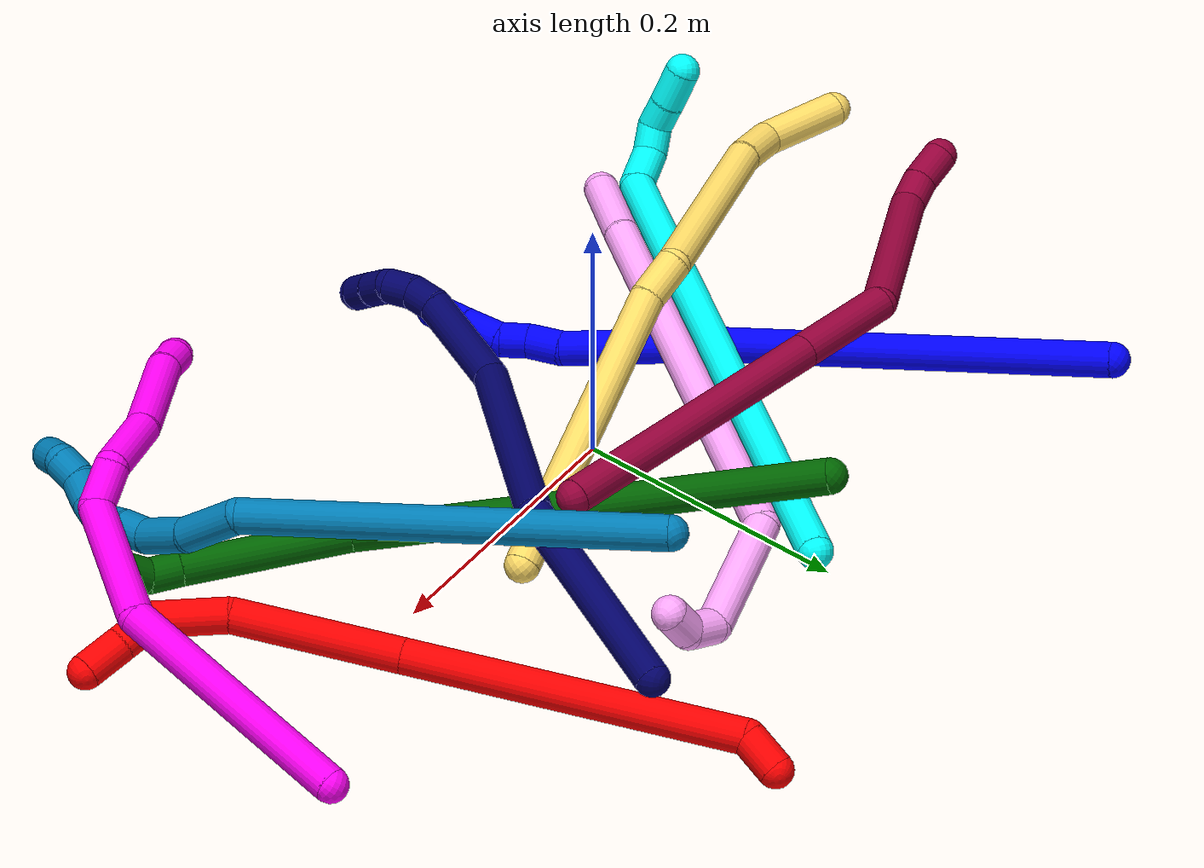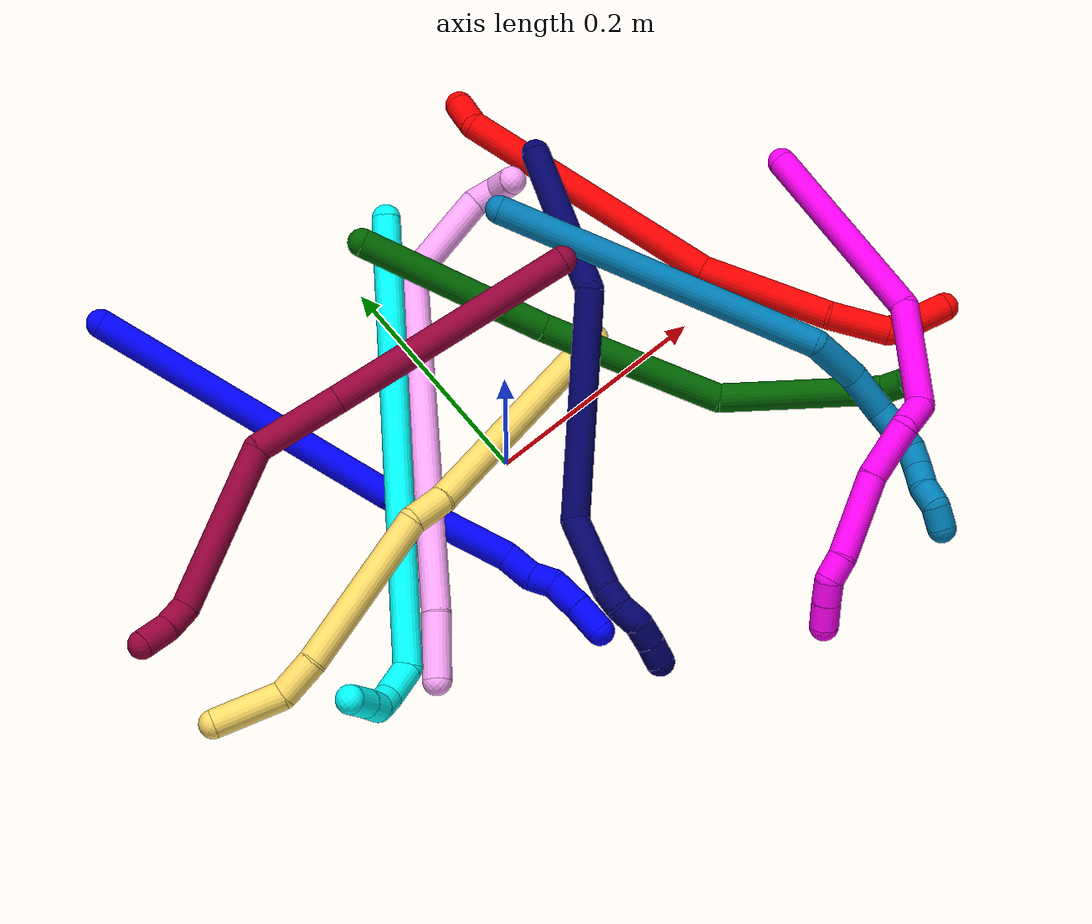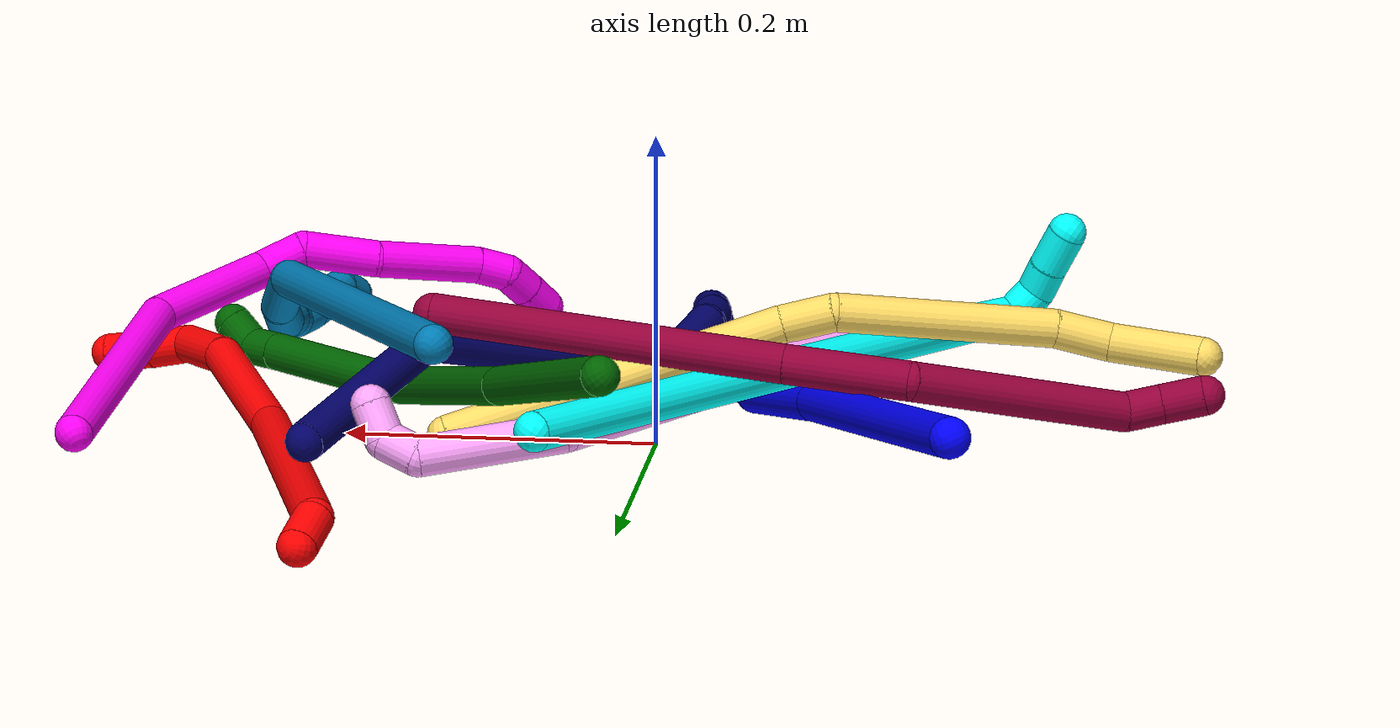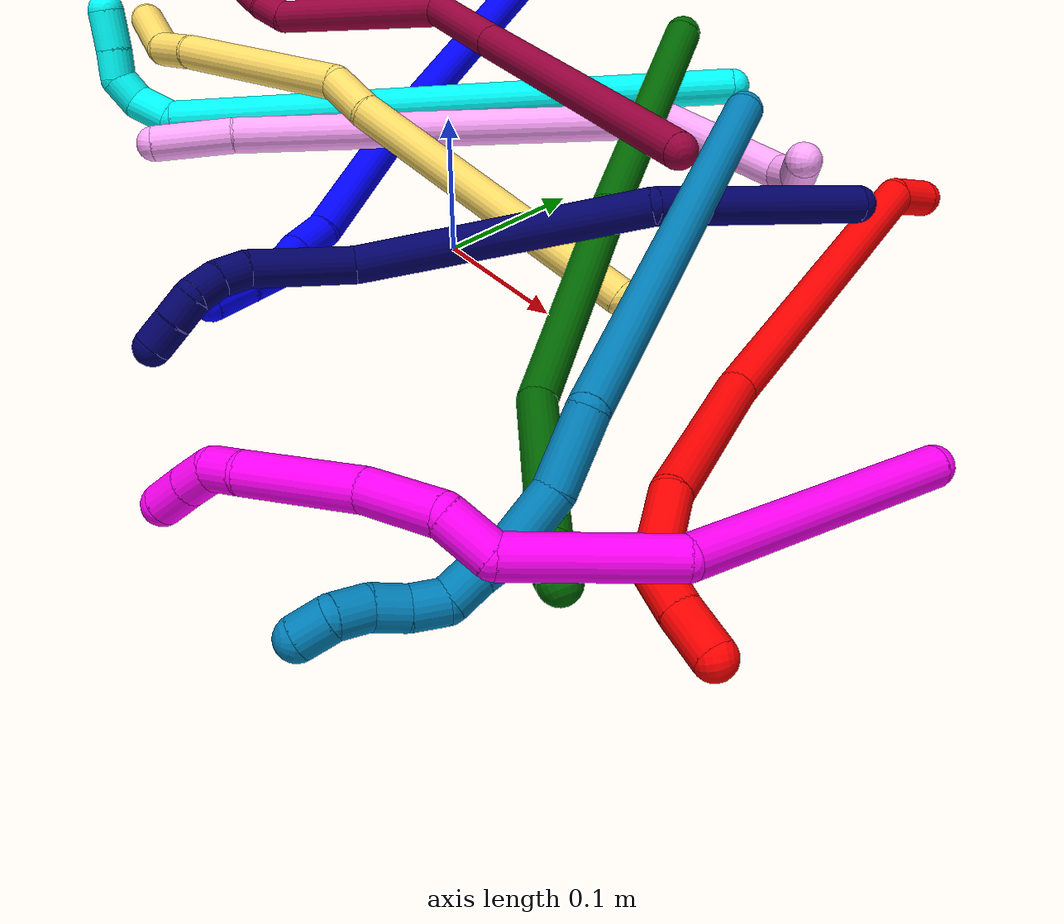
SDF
<sdf version="1.7">
 <world name="default">
  <plugin name="TubeGeneratorPlugin" filename="libtube_generator_plugin.so"/>
  <model name="photoneo_s_sensor">
   <static>1</static>
   <pose>0 0 2 1.57079 1.57079 3.14159</pose>
   <link name="link">
    <inertial><mass>0.1</mass></inertial>
    <sensor name="sensor" type="depth">
     <update_rate>30</update_rate>
     <camera>
      <horizontal_fov>1.22</horizontal_fov>
      <image><width>1920</width><height>1200</height><format>B8G8R8</format></image>
      <clip><near>0.1</near><far>4</far></clip>
      <depth_camera><output>points</output></depth_camera>
     </camera>
     <plugin name="camera_plugin" filename="libgazebo_ros_depth_camera.so">
      <baseline>0.2</baseline>
      <alwaysOn>1</alwaysOn>
      <updateRate>0.0</updateRate>
      <cameraName>camera_ir</cameraName>
      <imageTopicName>/camera/color/image_raw</imageTopicName>
      <cameraInfoTopicName>/camera/color/camera_info</cameraInfoTopicName>
      <depthImageTopicName>/camera/depth/image_raw</depthImageTopicName>
      <depthImageCameraInfoTopicName>/camera/depth/camera_info</depthImageCameraInfoTopicName>
      <pointCloudTopicName>/camera/depth/points</pointCloudTopicName>
      <frameName>fr_optical</frameName>
      <pointCloudCutoff>0.1</pointCloudCutoff>
      <pointCloudCutoffMax>2.0</pointCloudCutoffMax>
      <distortionK1>0</distortionK1>
      <distortionK2>0</distortionK2>
      <distortionK3>0</distortionK3>
      <distortionT1>0</distortionT1>
      <distortionT2>0</distortionT2>
      <CxPrime>0</CxPrime>
      <Cx>0</Cx>
      <Cy>0</Cy>
      <focalLength>0</focalLength>
      <hackBaseline>0</hackBaseline>
     </plugin>
    </sensor>
   </link>
  </model>
  <gravity>0 0 -9.8</gravity>
  <magnetic_field>6e-06 2.3e-05 -4.2e-05</magnetic_field>
  <atmosphere type="adiabatic"/>
  <physics name="default_physics" default="0" type="ode">
   <max_step_size>0.003</max_step_size>
   <real_time_factor>1</real_time_factor>
   <real_time_update_rate>1000</real_time_update_rate>
   <max_contacts>10000</max_contacts>
   <ode>
    <solver>
     <type>quick</type>
     <iters>100</iters>
     <sor>1.3</sor>
     <use_dynamic_moi_rescaling>0</use_dynamic_moi_rescaling>
    </solver>
    <constraints>
     <contact_max_correcting_vel>0</contact_max_correcting_vel>
     <contact_surface_layer>0.001</contact_surface_layer>
     <cfm>0</cfm>
     <erp>0.2</erp>
    </constraints>
   </ode>
  </physics>
  <scene><ambient>0.4 0.4 0.4 1</ambient><background>0.7 0.7 0.7 1</background><shadows>0</shadows></scene>
  <audio><device>default</device></audio>
  <spherical_coordinates>
   <surface_model>EARTH_WGS84</surface_model>
   <latitude_deg>0</latitude_deg>
   <longitude_deg>0</longitude_deg>
   <elevation>0</elevation>
   <heading_deg>0</heading_deg>
  </spherical_coordinates>
  <model name="bin">
   <static>1</static>
   <link name="bottom">
    <collision name="collision-bottom">
     <pose>0 0 -0.01 0 -0 0</pose>
     <geometry><box><size>0.8 0.6 0.02</size></box></geometry>
     <surface>
      <friction><ode><mu>100</mu><mu2>100</mu2></ode></friction>
      <contact><collide_bitmask>65535</collide_bitmask></contact>
     </surface>
    </collision>
   </link>
   <link name="west_wall">
    <collision name="collision-west_wall">
     <pose>-0.41 0 0.1 0 -0 0</pose>
     <geometry><box><size>0.02 0.6 0.2</size></box></geometry>
     <surface>
      <friction><ode><mu>100</mu><mu2>100</mu2></ode></friction>
      <contact><collide_bitmask>65535</collide_bitmask></contact>
     </surface>
    </collision>
   </link>
   <link name="east_wall">
    <collision name="collision-east_wall">
     <pose>0.41 0 0.1 0 -0 0</pose>
     <geometry><box><size>0.02 0.6 0.2</size></box></geometry>
     <surface>
      <friction><ode><mu>100</mu><mu2>100</mu2></ode></friction>
      <contact><collide_bitmask>65535</collide_bitmask></contact>
     </surface>
    </collision>
   </link>
   <link name="south_wall">
    <collision name="collision-south_wall">
     <pose>0 -0.31 0.1 0 -0 0</pose>
     <geometry><box><size>0.8 0.02 0.2</size></box></geometry>
     <surface>
      <friction><ode><mu>100</mu><mu2>100</mu2></ode></friction>
      <contact><collide_bitmask>65535</collide_bitmask></contact>
     </surface>
    </collision>
   </link>
   <link name="north_wall">
    <collision name="collision-north_wall">
     <pose>0 0.31 0.1 0 -0 0</pose>
     <geometry><box><size>0.8 0.02 0.2</size></box></geometry>
     <surface>
      <friction><ode><mu>100</mu><mu2>100</mu2></ode></friction>
      <contact><collide_bitmask>65535</collide_bitmask></contact>
     </surface>
    </collision>
   </link>
  </model>
  <model name="1">
   <static>0</static>
   <link name="1">
    <collision name="collision-cylinder-e_1_1_4">
     <pose>0.044806 -0.124741 -0.049137 1.94604 0.322525 0.469049</pose>
     <geometry><cylinder><radius>0.0125</radius><length>0.282719</length></cylinder></geometry>
     <surface>
      <friction><ode><mu>1.16</mu><mu2>1.16</mu2><slip1>0</slip1><slip2>0</slip2></ode></friction>
      <contact><ode><kp>1e+06</kp><kd>1</kd><max_vel>0</max_vel><min_depth>0.001</min_depth></ode></contact>
     </surface>
    </collision>
    <visual name="visual-cylinder-e_1_1_4">
     <pose>0.044806 -0.124741 -0.049137 1.94604 0.322525 0.469049</pose>
     <geometry><cylinder><radius>0.0125</radius><length>0.282719</length></cylinder></geometry>
     <material><ambient>0 0 1 1</ambient></material>
    </visual>
    <collision name="collision-cylinder-e_2_4_5">
     <pose>0.107243 -0.297546 -0.121761 2.02534 0.318395 0.503411</pose>
     <geometry><cylinder><radius>0.0125</radius><length>0.112651</length></cylinder></geometry>
     <surface>
      <friction><ode><mu>1.16</mu><mu2>1.16</mu2><slip1>0</slip1><slip2>0</slip2></ode></friction>
      <contact><ode><kp>1e+06</kp><kd>1</kd><max_vel>0</max_vel><min_depth>0.001</min_depth></ode></contact>
     </surface>
    </collision>
    <visual name="visual-cylinder-e_2_4_5">
     <pose>0.107243 -0.297546 -0.121761 2.02534 0.318395 0.503411</pose>
     <geometry><cylinder><radius>0.0125</radius><length>0.112651</length></cylinder></geometry>
     <material><ambient>0 0 1 1</ambient></material>
    </visual>
    <collision name="collision-cylinder-e_3_5_6">
     <pose>0.129277 -0.358056 -0.147484 1.74858 0.334919 0.398872</pose>
     <geometry><cylinder><radius>0.0125</radius><length>0.026782</length></cylinder></geometry>
     <surface>
      <friction><ode><mu>1.16</mu><mu2>1.16</mu2><slip1>0</slip1><slip2>0</slip2></ode></friction>
      <contact><ode><kp>1e+06</kp><kd>1</kd><max_vel>0</max_vel><min_depth>0.001</min_depth></ode></contact>
     </surface>
    </collision>
    <visual name="visual-cylinder-e_3_5_6">
     <pose>0.129277 -0.358056 -0.147484 1.74858 0.334919 0.398872</pose>
     <geometry><cylinder><radius>0.0125</radius><length>0.026782</length></cylinder></geometry>
     <material><ambient>0 0 1 1</ambient></material>
    </visual>
    <collision name="collision-cylinder-e_4_6_7">
     <pose>0.138938 -0.378118 -0.154255 2.10787 0.535561 0.899435</pose>
     <geometry><cylinder><radius>0.0125</radius><length>0.02061</length></cylinder></geometry>
     <surface>
      <friction><ode><mu>1.16</mu><mu2>1.16</mu2><slip1>0</slip1><slip2>0</slip2></ode></friction>
      <contact><ode><kp>1e+06</kp><kd>1</kd><max_vel>0</max_vel><min_depth>0.001</min_depth></ode></contact>
     </surface>
    </collision>
    <visual name="visual-cylinder-e_4_6_7">
     <pose>0.138938 -0.378118 -0.154255 2.10787 0.535561 0.899435</pose>
     <geometry><cylinder><radius>0.0125</radius><length>0.02061</length></cylinder></geometry>
     <material><ambient>0 0 1 1</ambient></material>
    </visual>
    <collision name="collision-cylinder-e_5_7_8">
     <pose>0.150076 -0.398813 -0.159052 1.59088 0.422314 0.430623</pose>
     <geometry><cylinder><radius>0.0125</radius><length>0.028687</length></cylinder></geometry>
     <surface>
      <friction><ode><mu>1.16</mu><mu2>1.16</mu2><slip1>0</slip1><slip2>0</slip2></ode></friction>
      <contact><ode><kp>1e+06</kp><kd>1</kd><max_vel>0</max_vel><min_depth>0.001</min_depth></ode></contact>
     </surface>
    </collision>
    <visual name="visual-cylinder-e_5_7_8">
     <pose>0.150076 -0.398813 -0.159052 1.59088 0.422314 0.430623</pose>
     <geometry><cylinder><radius>0.0125</radius><length>0.028687</length></cylinder></geometry>
     <material><ambient>0 0 1 1</ambient></material>
    </visual>
    <collision name="collision-cylinder-e_6_8_2">
     <pose>0.16087 -0.425291 -0.158906 1.54027 0.351476 0.341114</pose>
     <geometry><cylinder><radius>0.0125</radius><length>0.028552</length></cylinder></geometry>
     <surface>
      <friction><ode><mu>1.16</mu><mu2>1.16</mu2><slip1>0</slip1><slip2>0</slip2></ode></friction>
      <contact><ode><kp>1e+06</kp><kd>1</kd><max_vel>0</max_vel><min_depth>0.001</min_depth></ode></contact>
     </surface>
    </collision>
    <visual name="visual-cylinder-e_6_8_2">
     <pose>0.16087 -0.425291 -0.158906 1.54027 0.351476 0.341114</pose>
     <geometry><cylinder><radius>0.0125</radius><length>0.028552</length></cylinder></geometry>
     <material><ambient>0 0 1 1</ambient></material>
    </visual>
    <collision name="collision-sphere-2">
     <pose>0.165784 -0.438688 -0.158496 0 -0 0</pose>
     <geometry><sphere><radius>0.0125</radius></sphere></geometry>
     <surface>
      <friction><ode><mu>1.16</mu><mu2>1.16</mu2><slip1>0</slip1><slip2>0</slip2></ode></friction>
      <contact><ode><kp>1e+06</kp><kd>1</kd><max_vel>0</max_vel><min_depth>0.001</min_depth></ode></contact>
     </surface>
    </collision>
    <visual name="visual-sphere-2">
     <pose>0.165784 -0.438688 -0.158496 0 -0 0</pose>
     <geometry><sphere><radius>0.0125</radius></sphere></geometry>
     <material><ambient>0 0 1 1</ambient></material>
    </visual>
    <collision name="collision-sphere-4">
     <pose>0.089611 -0.249483 -0.098274 0 -0 0</pose>
     <geometry><sphere><radius>0.0125</radius></sphere></geometry>
     <surface>
      <friction><ode><mu>1.16</mu><mu2>1.16</mu2><slip1>0</slip1><slip2>0</slip2></ode></friction>
      <contact><ode><kp>1e+06</kp><kd>1</kd><max_vel>0</max_vel><min_depth>0.001</min_depth></ode></contact>
     </surface>
    </collision>
    <visual name="visual-sphere-4">
     <pose>0.089611 -0.249483 -0.098274 0 -0 0</pose>
     <geometry><sphere><radius>0.0125</radius></sphere></geometry>
     <material><ambient>0 0 1 1</ambient></material>
    </visual>
    <collision name="collision-sphere-1">
     <geometry><sphere><radius>0.0125</radius></sphere></geometry>
     <surface>
      <friction><ode><mu>1.16</mu><mu2>1.16</mu2><slip1>0</slip1><slip2>0</slip2></ode></friction>
      <contact><ode><kp>1e+06</kp><kd>1</kd><max_vel>0</max_vel><min_depth>0.001</min_depth></ode></contact>
     </surface>
    </collision>
    <visual name="visual-sphere-1">
     <geometry><sphere><radius>0.0125</radius></sphere></geometry>
     <material><ambient>0 0 1 1</ambient></material>
    </visual>
    <collision name="collision-sphere-8">
     <pose>0.155955 -0.411894 -0.159315 0 -0 0</pose>
     <geometry><sphere><radius>0.0125</radius></sphere></geometry>
     <surface>
      <friction><ode><mu>1.16</mu><mu2>1.16</mu2><slip1>0</slip1><slip2>0</slip2></ode></friction>
      <contact><ode><kp>1e+06</kp><kd>1</kd><max_vel>0</max_vel><min_depth>0.001</min_depth></ode></contact>
     </surface>
    </collision>
    <visual name="visual-sphere-8">
     <pose>0.155955 -0.411894 -0.159315 0 -0 0</pose>
     <geometry><sphere><radius>0.0125</radius></sphere></geometry>
     <material><ambient>0 0 1 1</ambient></material>
    </visual>
    <collision name="collision-sphere-5">
     <pose>0.124876 -0.345608 -0.145248 0 -0 0</pose>
     <geometry><sphere><radius>0.0125</radius></sphere></geometry>
     <surface>
      <friction><ode><mu>1.16</mu><mu2>1.16</mu2><slip1>0</slip1><slip2>0</slip2></ode></friction>
      <contact><ode><kp>1e+06</kp><kd>1</kd><max_vel>0</max_vel><min_depth>0.001</min_depth></ode></contact>
     </surface>
    </collision>
    <visual name="visual-sphere-5">
     <pose>0.124876 -0.345608 -0.145248 0 -0 0</pose>
     <geometry><sphere><radius>0.0125</radius></sphere></geometry>
     <material><ambient>0 0 1 1</ambient></material>
    </visual>
    <collision name="collision-sphere-6">
     <pose>0.133679 -0.370504 -0.149721 0 -0 0</pose>
     <geometry><sphere><radius>0.0125</radius></sphere></geometry>
     <surface>
      <friction><ode><mu>1.16</mu><mu2>1.16</mu2><slip1>0</slip1><slip2>0</slip2></ode></friction>
      <contact><ode><kp>1e+06</kp><kd>1</kd><max_vel>0</max_vel><min_depth>0.001</min_depth></ode></contact>
     </surface>
    </collision>
    <visual name="visual-sphere-6">
     <pose>0.133679 -0.370504 -0.149721 0 -0 0</pose>
     <geometry><sphere><radius>0.0125</radius></sphere></geometry>
     <material><ambient>0 0 1 1</ambient></material>
    </visual>
    <collision name="collision-sphere-7">
     <pose>0.144196 -0.385732 -0.158789 0 -0 0</pose>
     <geometry><sphere><radius>0.0125</radius></sphere></geometry>
     <surface>
      <friction><ode><mu>1.16</mu><mu2>1.16</mu2><slip1>0</slip1><slip2>0</slip2></ode></friction>
      <contact><ode><kp>1e+06</kp><kd>1</kd><max_vel>0</max_vel><min_depth>0.001</min_depth></ode></contact>
     </surface>
    </collision>
    <visual name="visual-sphere-7">
     <pose>0.144196 -0.385732 -0.158789 0 -0 0</pose>
     <geometry><sphere><radius>0.0125</radius></sphere></geometry>
     <material><ambient>0 0 1 1</ambient></material>
    </visual>
    <inertial>
     <pose>0.079945 -0.219503 -0.087675 0 -0 0</pose>
     <mass>0.5</mass>
     <inertia>
      <ixx>0.002599</ixx>
      <ixy>0</ixy>
      <ixz>0</ixz>
      <iyy>0.000442</iyy>
      <iyz>0</iyz>
      <izz>0.001131</izz>
     </inertia>
    </inertial>
   </link>
   <pose>-0.206307 0.288518 0.093998 0.722694 -0.997491 -0.738272</pose>
  </model>
  <model name="2">
   <static>0</static>
   <link name="2">
    <collision name="collision-cylinder-e_1_1_4">
     <pose>0.007827 -0.006777 0.009974 0.596817 0.575712 0.181643</pose>
     <geometry><cylinder><radius>0.0125</radius><length>0.028752</length></cylinder></geometry>
     <surface>
      <friction><ode><mu>1.16</mu><mu2>1.16</mu2><slip1>0</slip1><slip2>0</slip2></ode></friction>
      <contact><ode><kp>1e+06</kp><kd>1</kd><max_vel>0</max_vel><min_depth>0.001</min_depth></ode></contact>
     </surface>
    </collision>
    <visual name="visual-cylinder-e_1_1_4">
     <pose>0.007827 -0.006777 0.009974 0.596817 0.575712 0.181643</pose>
     <geometry><cylinder><radius>0.0125</radius><length>0.028752</length></cylinder></geometry>
     <material><ambient>1 0 0 1</ambient></material>
    </visual>
    <collision name="collision-cylinder-e_2_4_5">
     <pose>0.027157 -0.116205 0.082884 1.0208 0.095246 0.053354</pose>
     <geometry><cylinder><radius>0.0125</radius><length>0.241914</length></cylinder></geometry>
     <surface>
      <friction><ode><mu>1.16</mu><mu2>1.16</mu2><slip1>0</slip1><slip2>0</slip2></ode></friction>
      <contact><ode><kp>1e+06</kp><kd>1</kd><max_vel>0</max_vel><min_depth>0.001</min_depth></ode></contact>
     </surface>
    </collision>
    <visual name="visual-cylinder-e_2_4_5">
     <pose>0.027157 -0.116205 0.082884 1.0208 0.095246 0.053354</pose>
     <geometry><cylinder><radius>0.0125</radius><length>0.241914</length></cylinder></geometry>
     <material><ambient>1 0 0 1</ambient></material>
    </visual>
    <collision name="collision-cylinder-e_3_5_6">
     <pose>0.052136 -0.272971 0.165832 1.21657 0.229455 0.160147</pose>
     <geometry><cylinder><radius>0.0125</radius><length>0.118497</length></cylinder></geometry>
     <surface>
      <friction><ode><mu>1.16</mu><mu2>1.16</mu2><slip1>0</slip1><slip2>0</slip2></ode></friction>
      <contact><ode><kp>1e+06</kp><kd>1</kd><max_vel>0</max_vel><min_depth>0.001</min_depth></ode></contact>
     </surface>
    </collision>
    <visual name="visual-cylinder-e_3_5_6">
     <pose>0.052136 -0.272971 0.165832 1.21657 0.229455 0.160147</pose>
     <geometry><cylinder><radius>0.0125</radius><length>0.118497</length></cylinder></geometry>
     <material><ambient>1 0 0 1</ambient></material>
    </visual>
    <collision name="collision-cylinder-e_4_6_7">
     <pose>0.064855 -0.352868 0.191812 1.34338 -0.028588 -0.022728</pose>
     <geometry><cylinder><radius>0.0125</radius><length>0.052951</length></cylinder></geometry>
     <surface>
      <friction><ode><mu>1.16</mu><mu2>1.16</mu2><slip1>0</slip1><slip2>0</slip2></ode></friction>
      <contact><ode><kp>1e+06</kp><kd>1</kd><max_vel>0</max_vel><min_depth>0.001</min_depth></ode></contact>
     </surface>
    </collision>
    <visual name="visual-cylinder-e_4_6_7">
     <pose>0.064855 -0.352868 0.191812 1.34338 -0.028588 -0.022728</pose>
     <geometry><cylinder><radius>0.0125</radius><length>0.052951</length></cylinder></geometry>
     <material><ambient>1 0 0 1</ambient></material>
    </visual>
    <collision name="collision-cylinder-e_5_7_8">
     <pose>0.059578 -0.390214 0.19252 1.99757 -0.341877 -0.52393</pose>
     <geometry><cylinder><radius>0.0125</radius><length>0.026966</length></cylinder></geometry>
     <surface>
      <friction><ode><mu>1.16</mu><mu2>1.16</mu2><slip1>0</slip1><slip2>0</slip2></ode></friction>
      <contact><ode><kp>1e+06</kp><kd>1</kd><max_vel>0</max_vel><min_depth>0.001</min_depth></ode></contact>
     </surface>
    </collision>
    <visual name="visual-cylinder-e_5_7_8">
     <pose>0.059578 -0.390214 0.19252 1.99757 -0.341877 -0.52393</pose>
     <geometry><cylinder><radius>0.0125</radius><length>0.026966</length></cylinder></geometry>
     <material><ambient>1 0 0 1</ambient></material>
    </visual>
    <collision name="collision-cylinder-e_6_8_2">
     <pose>0.050822 -0.414843 0.180164 2.0685 -0.277488 -0.46123</pose>
     <geometry><cylinder><radius>0.0125</radius><length>0.03092</length></cylinder></geometry>
     <surface>
      <friction><ode><mu>1.16</mu><mu2>1.16</mu2><slip1>0</slip1><slip2>0</slip2></ode></friction>
      <contact><ode><kp>1e+06</kp><kd>1</kd><max_vel>0</max_vel><min_depth>0.001</min_depth></ode></contact>
     </surface>
    </collision>
    <visual name="visual-cylinder-e_6_8_2">
     <pose>0.050822 -0.414843 0.180164 2.0685 -0.277488 -0.46123</pose>
     <geometry><cylinder><radius>0.0125</radius><length>0.03092</length></cylinder></geometry>
     <material><ambient>1 0 0 1</ambient></material>
    </visual>
    <collision name="collision-sphere-2">
     <pose>0.046587 -0.427907 0.173065 0 -0 0</pose>
     <geometry><sphere><radius>0.0125</radius></sphere></geometry>
     <surface>
      <friction><ode><mu>1.16</mu><mu2>1.16</mu2><slip1>0</slip1><slip2>0</slip2></ode></friction>
      <contact><ode><kp>1e+06</kp><kd>1</kd><max_vel>0</max_vel><min_depth>0.001</min_depth></ode></contact>
     </surface>
    </collision>
    <visual name="visual-sphere-2">
     <pose>0.046587 -0.427907 0.173065 0 -0 0</pose>
     <geometry><sphere><radius>0.0125</radius></sphere></geometry>
     <material><ambient>1 0 0 1</ambient></material>
    </visual>
    <collision name="collision-sphere-4">
     <pose>0.015653 -0.013554 0.019948 0 -0 0</pose>
     <geometry><sphere><radius>0.0125</radius></sphere></geometry>
     <surface>
      <friction><ode><mu>1.16</mu><mu2>1.16</mu2><slip1>0</slip1><slip2>0</slip2></ode></friction>
      <contact><ode><kp>1e+06</kp><kd>1</kd><max_vel>0</max_vel><min_depth>0.001</min_depth></ode></contact>
     </surface>
    </collision>
    <visual name="visual-sphere-4">
     <pose>0.015653 -0.013554 0.019948 0 -0 0</pose>
     <geometry><sphere><radius>0.0125</radius></sphere></geometry>
     <material><ambient>1 0 0 1</ambient></material>
    </visual>
    <collision name="collision-sphere-1">
     <geometry><sphere><radius>0.0125</radius></sphere></geometry>
     <surface>
      <friction><ode><mu>1.16</mu><mu2>1.16</mu2><slip1>0</slip1><slip2>0</slip2></ode></friction>
      <contact><ode><kp>1e+06</kp><kd>1</kd><max_vel>0</max_vel><min_depth>0.001</min_depth></ode></contact>
     </surface>
    </collision>
    <visual name="visual-sphere-1">
     <geometry><sphere><radius>0.0125</radius></sphere></geometry>
     <material><ambient>1 0 0 1</ambient></material>
    </visual>
    <collision name="collision-sphere-8">
     <pose>0.055058 -0.401778 0.187262 0 -0 0</pose>
     <geometry><sphere><radius>0.0125</radius></sphere></geometry>
     <surface>
      <friction><ode><mu>1.16</mu><mu2>1.16</mu2><slip1>0</slip1><slip2>0</slip2></ode></friction>
      <contact><ode><kp>1e+06</kp><kd>1</kd><max_vel>0</max_vel><min_depth>0.001</min_depth></ode></contact>
     </surface>
    </collision>
    <visual name="visual-sphere-8">
     <pose>0.055058 -0.401778 0.187262 0 -0 0</pose>
     <geometry><sphere><radius>0.0125</radius></sphere></geometry>
     <material><ambient>1 0 0 1</ambient></material>
    </visual>
    <collision name="collision-sphere-5">
     <pose>0.03866 -0.218857 0.14582 0 -0 0</pose>
     <geometry><sphere><radius>0.0125</radius></sphere></geometry>
     <surface>
      <friction><ode><mu>1.16</mu><mu2>1.16</mu2><slip1>0</slip1><slip2>0</slip2></ode></friction>
      <contact><ode><kp>1e+06</kp><kd>1</kd><max_vel>0</max_vel><min_depth>0.001</min_depth></ode></contact>
     </surface>
    </collision>
    <visual name="visual-sphere-5">
     <pose>0.03866 -0.218857 0.14582 0 -0 0</pose>
     <geometry><sphere><radius>0.0125</radius></sphere></geometry>
     <material><ambient>1 0 0 1</ambient></material>
    </visual>
    <collision name="collision-sphere-6">
     <pose>0.065612 -0.327084 0.185845 0 -0 0</pose>
     <geometry><sphere><radius>0.0125</radius></sphere></geometry>
     <surface>
      <friction><ode><mu>1.16</mu><mu2>1.16</mu2><slip1>0</slip1><slip2>0</slip2></ode></friction>
      <contact><ode><kp>1e+06</kp><kd>1</kd><max_vel>0</max_vel><min_depth>0.001</min_depth></ode></contact>
     </surface>
    </collision>
    <visual name="visual-sphere-6">
     <pose>0.065612 -0.327084 0.185845 0 -0 0</pose>
     <geometry><sphere><radius>0.0125</radius></sphere></geometry>
     <material><ambient>1 0 0 1</ambient></material>
    </visual>
    <collision name="collision-sphere-7">
     <pose>0.064098 -0.378651 0.197778 0 -0 0</pose>
     <geometry><sphere><radius>0.0125</radius></sphere></geometry>
     <surface>
      <friction><ode><mu>1.16</mu><mu2>1.16</mu2><slip1>0</slip1><slip2>0</slip2></ode></friction>
      <contact><ode><kp>1e+06</kp><kd>1</kd><max_vel>0</max_vel><min_depth>0.001</min_depth></ode></contact>
     </surface>
    </collision>
    <visual name="visual-sphere-7">
     <pose>0.064098 -0.378651 0.197778 0 -0 0</pose>
     <geometry><sphere><radius>0.0125</radius></sphere></geometry>
     <material><ambient>1 0 0 1</ambient></material>
    </visual>
    <inertial>
     <pose>0.039169 -0.205374 0.121814 0 -0 0</pose>
     <mass>0.5</mass>
     <inertia>
      <ixx>0.001429</ixx>
      <ixy>0</ixy>
      <ixz>0</ixz>
      <iyy>0.000733</iyy>
      <iyz>0</iyz>
      <izz>0.00103</izz>
     </inertia>
    </inertial>
   </link>
   <pose>0.178473 0.284062 0.012043 3.12868 -1.31276 -2.27677</pose>
  </model>
  <model name="3">
   <static>0</static>
   <link name="3">
    <collision name="collision-cylinder-e_1_1_4">
     <pose>-0.157918 0.092777 -0.081291 -2.29031 -0.907674 1.64394</pose>
     <geometry><cylinder><radius>0.0125</radius><length>0.400768</length></cylinder></geometry>
     <surface>
      <friction><ode><mu>1.16</mu><mu2>1.16</mu2><slip1>0</slip1><slip2>0</slip2></ode></friction>
      <contact><ode><kp>1e+06</kp><kd>1</kd><max_vel>0</max_vel><min_depth>0.001</min_depth></ode></contact>
     </surface>
    </collision>
    <visual name="visual-cylinder-e_1_1_4">
     <pose>-0.157918 0.092777 -0.081291 -2.29031 -0.907674 1.64394</pose>
     <geometry><cylinder><radius>0.0125</radius><length>0.400768</length></cylinder></geometry>
     <material><ambient>0.003922 1 0.996078 1</ambient></material>
    </visual>
    <collision name="collision-cylinder-e_2_4_5">
     <pose>-0.319981 0.196244 -0.172913 -2.33911 -0.27198 0.623987</pose>
     <geometry><cylinder><radius>0.0125</radius><length>0.030866</length></cylinder></geometry>
     <surface>
      <friction><ode><mu>1.16</mu><mu2>1.16</mu2><slip1>0</slip1><slip2>0</slip2></ode></friction>
      <contact><ode><kp>1e+06</kp><kd>1</kd><max_vel>0</max_vel><min_depth>0.001</min_depth></ode></contact>
     </surface>
    </collision>
    <visual name="visual-cylinder-e_2_4_5">
     <pose>-0.319981 0.196244 -0.172913 -2.33911 -0.27198 0.623987</pose>
     <geometry><cylinder><radius>0.0125</radius><length>0.030866</length></cylinder></geometry>
     <material><ambient>0.003922 1 0.996078 1</ambient></material>
    </visual>
    <collision name="collision-cylinder-e_3_5_6">
     <pose>-0.325053 0.217179 -0.185098 -1.74988 -0.088669 0.106131</pose>
     <geometry><cylinder><radius>0.0125</radius><length>0.020907</length></cylinder></geometry>
     <surface>
      <friction><ode><mu>1.16</mu><mu2>1.16</mu2><slip1>0</slip1><slip2>0</slip2></ode></friction>
      <contact><ode><kp>1e+06</kp><kd>1</kd><max_vel>0</max_vel><min_depth>0.001</min_depth></ode></contact>
     </surface>
    </collision>
    <visual name="visual-cylinder-e_3_5_6">
     <pose>-0.325053 0.217179 -0.185098 -1.74988 -0.088669 0.106131</pose>
     <geometry><cylinder><radius>0.0125</radius><length>0.020907</length></cylinder></geometry>
     <material><ambient>0.003922 1 0.996078 1</ambient></material>
    </visual>
    <collision name="collision-cylinder-e_4_6_7">
     <pose>-0.321513 0.236446 -0.186112 -1.47783 0.457916 -0.41844</pose>
     <geometry><cylinder><radius>0.0125</radius><length>0.020201</length></cylinder></geometry>
     <surface>
      <friction><ode><mu>1.16</mu><mu2>1.16</mu2><slip1>0</slip1><slip2>0</slip2></ode></friction>
      <contact><ode><kp>1e+06</kp><kd>1</kd><max_vel>0</max_vel><min_depth>0.001</min_depth></ode></contact>
     </surface>
    </collision>
    <visual name="visual-cylinder-e_4_6_7">
     <pose>-0.321513 0.236446 -0.186112 -1.47783 0.457916 -0.41844</pose>
     <geometry><cylinder><radius>0.0125</radius><length>0.020201</length></cylinder></geometry>
     <material><ambient>0.003922 1 0.996078 1</ambient></material>
    </visual>
    <collision name="collision-cylinder-e_5_7_2">
     <pose>-0.311674 0.25797 -0.184534 -1.51197 0.405271 -0.382682</pose>
     <geometry><cylinder><radius>0.0125</radius><length>0.027258</length></cylinder></geometry>
     <surface>
      <friction><ode><mu>1.16</mu><mu2>1.16</mu2><slip1>0</slip1><slip2>0</slip2></ode></friction>
      <contact><ode><kp>1e+06</kp><kd>1</kd><max_vel>0</max_vel><min_depth>0.001</min_depth></ode></contact>
     </surface>
    </collision>
    <visual name="visual-cylinder-e_5_7_2">
     <pose>-0.311674 0.25797 -0.184534 -1.51197 0.405271 -0.382682</pose>
     <geometry><cylinder><radius>0.0125</radius><length>0.027258</length></cylinder></geometry>
     <material><ambient>0.003922 1 0.996078 1</ambient></material>
    </visual>
    <collision name="collision-sphere-2">
     <pose>-0.306301 0.270473 -0.183798 0 -0 0</pose>
     <geometry><sphere><radius>0.0125</radius></sphere></geometry>
     <surface>
      <friction><ode><mu>1.16</mu><mu2>1.16</mu2><slip1>0</slip1><slip2>0</slip2></ode></friction>
      <contact><ode><kp>1e+06</kp><kd>1</kd><max_vel>0</max_vel><min_depth>0.001</min_depth></ode></contact>
     </surface>
    </collision>
    <visual name="visual-sphere-2">
     <pose>-0.306301 0.270473 -0.183798 0 -0 0</pose>
     <geometry><sphere><radius>0.0125</radius></sphere></geometry>
     <material><ambient>0.003922 1 0.996078 1</ambient></material>
    </visual>
    <collision name="collision-sphere-7">
     <pose>-0.317048 0.245467 -0.185271 0 -0 0</pose>
     <geometry><sphere><radius>0.0125</radius></sphere></geometry>
     <surface>
      <friction><ode><mu>1.16</mu><mu2>1.16</mu2><slip1>0</slip1><slip2>0</slip2></ode></friction>
      <contact><ode><kp>1e+06</kp><kd>1</kd><max_vel>0</max_vel><min_depth>0.001</min_depth></ode></contact>
     </surface>
    </collision>
    <visual name="visual-sphere-7">
     <pose>-0.317048 0.245467 -0.185271 0 -0 0</pose>
     <geometry><sphere><radius>0.0125</radius></sphere></geometry>
     <material><ambient>0.003922 1 0.996078 1</ambient></material>
    </visual>
    <collision name="collision-sphere-6">
     <pose>-0.325978 0.227425 -0.186953 0 -0 0</pose>
     <geometry><sphere><radius>0.0125</radius></sphere></geometry>
     <surface>
      <friction><ode><mu>1.16</mu><mu2>1.16</mu2><slip1>0</slip1><slip2>0</slip2></ode></friction>
      <contact><ode><kp>1e+06</kp><kd>1</kd><max_vel>0</max_vel><min_depth>0.001</min_depth></ode></contact>
     </surface>
    </collision>
    <visual name="visual-sphere-6">
     <pose>-0.325978 0.227425 -0.186953 0 -0 0</pose>
     <geometry><sphere><radius>0.0125</radius></sphere></geometry>
     <material><ambient>0.003922 1 0.996078 1</ambient></material>
    </visual>
    <collision name="collision-sphere-5">
     <pose>-0.324127 0.206933 -0.183244 0 -0 0</pose>
     <geometry><sphere><radius>0.0125</radius></sphere></geometry>
     <surface>
      <friction><ode><mu>1.16</mu><mu2>1.16</mu2><slip1>0</slip1><slip2>0</slip2></ode></friction>
      <contact><ode><kp>1e+06</kp><kd>1</kd><max_vel>0</max_vel><min_depth>0.001</min_depth></ode></contact>
     </surface>
    </collision>
    <visual name="visual-sphere-5">
     <pose>-0.324127 0.206933 -0.183244 0 -0 0</pose>
     <geometry><sphere><radius>0.0125</radius></sphere></geometry>
     <material><ambient>0.003922 1 0.996078 1</ambient></material>
    </visual>
    <collision name="collision-sphere-1">
     <geometry><sphere><radius>0.0125</radius></sphere></geometry>
     <surface>
      <friction><ode><mu>1.16</mu><mu2>1.16</mu2><slip1>0</slip1><slip2>0</slip2></ode></friction>
      <contact><ode><kp>1e+06</kp><kd>1</kd><max_vel>0</max_vel><min_depth>0.001</min_depth></ode></contact>
     </surface>
    </collision>
    <visual name="visual-sphere-1">
     <geometry><sphere><radius>0.0125</radius></sphere></geometry>
     <material><ambient>0.003922 1 0.996078 1</ambient></material>
    </visual>
    <collision name="collision-sphere-4">
     <pose>-0.315835 0.185554 -0.162583 0 -0 0</pose>
     <geometry><sphere><radius>0.0125</radius></sphere></geometry>
     <surface>
      <friction><ode><mu>1.16</mu><mu2>1.16</mu2><slip1>0</slip1><slip2>0</slip2></ode></friction>
      <contact><ode><kp>1e+06</kp><kd>1</kd><max_vel>0</max_vel><min_depth>0.001</min_depth></ode></contact>
     </surface>
    </collision>
    <visual name="visual-sphere-4">
     <pose>-0.315835 0.185554 -0.162583 0 -0 0</pose>
     <geometry><sphere><radius>0.0125</radius></sphere></geometry>
     <material><ambient>0.003922 1 0.996078 1</ambient></material>
    </visual>
    <inertial>
     <pose>-0.189902 0.119176 -0.101151 0 -0 0</pose>
     <mass>0.5</mass>
     <inertia>
      <ixx>0.003046</ixx>
      <ixy>0</ixy>
      <ixz>0</ixz>
      <iyy>0.006763</iyy>
      <iyz>0</iyz>
      <izz>0.001726</izz>
     </inertia>
    </inertial>
   </link>
   <pose>0.046214 0.21968 0.069163 1.01726 -0.26126 1.56939</pose>
  </model>
  <model name="4">
   <static>0</static>
   <link name="4">
    <collision name="collision-cylinder-e_1_1_4">
     <pose>0.005935 0.020909 0.018339 -0.850787 0.210249 -0.095534</pose>
     <geometry><cylinder><radius>0.0125</radius><length>0.056876</length></cylinder></geometry>
     <surface>
      <friction><ode><mu>1.16</mu><mu2>1.16</mu2><slip1>0</slip1><slip2>0</slip2></ode></friction>
      <contact><ode><kp>1e+06</kp><kd>1</kd><max_vel>0</max_vel><min_depth>0.001</min_depth></ode></contact>
     </surface>
    </collision>
    <visual name="visual-cylinder-e_1_1_4">
     <pose>0.005935 0.020909 0.018339 -0.850787 0.210249 -0.095534</pose>
     <geometry><cylinder><radius>0.0125</radius><length>0.056876</length></cylinder></geometry>
     <material><ambient>1 0.65098 0.996078 1</ambient></material>
    </visual>
    <collision name="collision-cylinder-e_2_4_5">
     <pose>0.057676 0.159073 0.123817 -0.931688 0.303838 -0.153637</pose>
     <geometry><cylinder><radius>0.0125</radius><length>0.306203</length></cylinder></geometry>
     <surface>
      <friction><ode><mu>1.16</mu><mu2>1.16</mu2><slip1>0</slip1><slip2>0</slip2></ode></friction>
      <contact><ode><kp>1e+06</kp><kd>1</kd><max_vel>0</max_vel><min_depth>0.001</min_depth></ode></contact>
     </surface>
    </collision>
    <visual name="visual-cylinder-e_2_4_5">
     <pose>0.057676 0.159073 0.123817 -0.931688 0.303838 -0.153637</pose>
     <geometry><cylinder><radius>0.0125</radius><length>0.306203</length></cylinder></geometry>
     <material><ambient>1 0.65098 0.996078 1</ambient></material>
    </visual>
    <collision name="collision-cylinder-e_3_5_6">
     <pose>0.125119 0.284064 0.249843 -0.196391 0.499557 -0.050252</pose>
     <geometry><cylinder><radius>0.0125</radius><length>0.09034</length></cylinder></geometry>
     <surface>
      <friction><ode><mu>1.16</mu><mu2>1.16</mu2><slip1>0</slip1><slip2>0</slip2></ode></friction>
      <contact><ode><kp>1e+06</kp><kd>1</kd><max_vel>0</max_vel><min_depth>0.001</min_depth></ode></contact>
     </surface>
    </collision>
    <visual name="visual-cylinder-e_3_5_6">
     <pose>0.125119 0.284064 0.249843 -0.196391 0.499557 -0.050252</pose>
     <geometry><cylinder><radius>0.0125</radius><length>0.09034</length></cylinder></geometry>
     <material><ambient>1 0.65098 0.996078 1</ambient></material>
    </visual>
    <collision name="collision-cylinder-e_4_6_7">
     <pose>0.146274 0.288555 0.299898 0.282945 -0.041565 -0.005921</pose>
     <geometry><cylinder><radius>0.0125</radius><length>0.023279</length></cylinder></geometry>
     <surface>
      <friction><ode><mu>1.16</mu><mu2>1.16</mu2><slip1>0</slip1><slip2>0</slip2></ode></friction>
      <contact><ode><kp>1e+06</kp><kd>1</kd><max_vel>0</max_vel><min_depth>0.001</min_depth></ode></contact>
     </surface>
    </collision>
    <visual name="visual-cylinder-e_4_6_7">
     <pose>0.146274 0.288555 0.299898 0.282945 -0.041565 -0.005921</pose>
     <geometry><cylinder><radius>0.0125</radius><length>0.023279</length></cylinder></geometry>
     <material><ambient>1 0.65098 0.996078 1</ambient></material>
    </visual>
    <collision name="collision-cylinder-e_5_7_2">
     <pose>0.137888 0.281837 0.318891 0.417451 -0.745418 -0.165252</pose>
     <geometry><cylinder><radius>0.0125</radius><length>0.023302</length></cylinder></geometry>
     <surface>
      <friction><ode><mu>1.16</mu><mu2>1.16</mu2><slip1>0</slip1><slip2>0</slip2></ode></friction>
      <contact><ode><kp>1e+06</kp><kd>1</kd><max_vel>0</max_vel><min_depth>0.001</min_depth></ode></contact>
     </surface>
    </collision>
    <visual name="visual-cylinder-e_5_7_2">
     <pose>0.137888 0.281837 0.318891 0.417451 -0.745418 -0.165252</pose>
     <geometry><cylinder><radius>0.0125</radius><length>0.023302</length></cylinder></geometry>
     <material><ambient>1 0.65098 0.996078 1</ambient></material>
    </visual>
    <collision name="collision-sphere-2">
     <pose>0.129985 0.278366 0.326717 0 -0 0</pose>
     <geometry><sphere><radius>0.0125</radius></sphere></geometry>
     <surface>
      <friction><ode><mu>1.16</mu><mu2>1.16</mu2><slip1>0</slip1><slip2>0</slip2></ode></friction>
      <contact><ode><kp>1e+06</kp><kd>1</kd><max_vel>0</max_vel><min_depth>0.001</min_depth></ode></contact>
     </surface>
    </collision>
    <visual name="visual-sphere-2">
     <pose>0.129985 0.278366 0.326717 0 -0 0</pose>
     <geometry><sphere><radius>0.0125</radius></sphere></geometry>
     <material><ambient>1 0.65098 0.996078 1</ambient></material>
    </visual>
    <collision name="collision-sphere-7">
     <pose>0.14579 0.285308 0.311065 0 -0 0</pose>
     <geometry><sphere><radius>0.0125</radius></sphere></geometry>
     <surface>
      <friction><ode><mu>1.16</mu><mu2>1.16</mu2><slip1>0</slip1><slip2>0</slip2></ode></friction>
      <contact><ode><kp>1e+06</kp><kd>1</kd><max_vel>0</max_vel><min_depth>0.001</min_depth></ode></contact>
     </surface>
    </collision>
    <visual name="visual-sphere-7">
     <pose>0.14579 0.285308 0.311065 0 -0 0</pose>
     <geometry><sphere><radius>0.0125</radius></sphere></geometry>
     <material><ambient>1 0.65098 0.996078 1</ambient></material>
    </visual>
    <collision name="collision-sphere-6">
     <pose>0.146758 0.291801 0.288731 0 -0 0</pose>
     <geometry><sphere><radius>0.0125</radius></sphere></geometry>
     <surface>
      <friction><ode><mu>1.16</mu><mu2>1.16</mu2><slip1>0</slip1><slip2>0</slip2></ode></friction>
      <contact><ode><kp>1e+06</kp><kd>1</kd><max_vel>0</max_vel><min_depth>0.001</min_depth></ode></contact>
     </surface>
    </collision>
    <visual name="visual-sphere-6">
     <pose>0.146758 0.291801 0.288731 0 -0 0</pose>
     <geometry><sphere><radius>0.0125</radius></sphere></geometry>
     <material><ambient>1 0.65098 0.996078 1</ambient></material>
    </visual>
    <collision name="collision-sphere-5">
     <pose>0.103481 0.276328 0.210956 0 -0 0</pose>
     <geometry><sphere><radius>0.0125</radius></sphere></geometry>
     <surface>
      <friction><ode><mu>1.16</mu><mu2>1.16</mu2><slip1>0</slip1><slip2>0</slip2></ode></friction>
      <contact><ode><kp>1e+06</kp><kd>1</kd><max_vel>0</max_vel><min_depth>0.001</min_depth></ode></contact>
     </surface>
    </collision>
    <visual name="visual-sphere-5">
     <pose>0.103481 0.276328 0.210956 0 -0 0</pose>
     <geometry><sphere><radius>0.0125</radius></sphere></geometry>
     <material><ambient>1 0.65098 0.996078 1</ambient></material>
    </visual>
    <collision name="collision-sphere-1">
     <geometry><sphere><radius>0.0125</radius></sphere></geometry>
     <surface>
      <friction><ode><mu>1.16</mu><mu2>1.16</mu2><slip1>0</slip1><slip2>0</slip2></ode></friction>
      <contact><ode><kp>1e+06</kp><kd>1</kd><max_vel>0</max_vel><min_depth>0.001</min_depth></ode></contact>
     </surface>
    </collision>
    <visual name="visual-sphere-1">
     <geometry><sphere><radius>0.0125</radius></sphere></geometry>
     <material><ambient>1 0.65098 0.996078 1</ambient></material>
    </visual>
    <collision name="collision-sphere-4">
     <pose>0.01187 0.041818 0.036678 0 -0 0</pose>
     <geometry><sphere><radius>0.0125</radius></sphere></geometry>
     <surface>
      <friction><ode><mu>1.16</mu><mu2>1.16</mu2><slip1>0</slip1><slip2>0</slip2></ode></friction>
      <contact><ode><kp>1e+06</kp><kd>1</kd><max_vel>0</max_vel><min_depth>0.001</min_depth></ode></contact>
     </surface>
    </collision>
    <visual name="visual-sphere-4">
     <pose>0.01187 0.041818 0.036678 0 -0 0</pose>
     <geometry><sphere><radius>0.0125</radius></sphere></geometry>
     <material><ambient>1 0.65098 0.996078 1</ambient></material>
    </visual>
    <inertial>
     <pose>0.071839 0.177689 0.151878 0 -0 0</pose>
     <mass>0.5</mass>
     <inertia>
      <ixx>0.001999</ixx>
      <ixy>0</ixy>
      <ixz>0</ixz>
      <iyy>0.001251</iyy>
      <iyz>0</iyz>
      <izz>-0.002592</izz>
     </inertia>
    </inertial>
   </link>
   <pose>-0.176896 -0.125869 0.051341 0.257788 1.1996 0.318409</pose>
  </model>
  <model name="5">
   <static>0</static>
   <link name="5">
    <collision name="collision-cylinder-e_1_1_4">
     <pose>-0.07071 0.047085 -0.072844 -2.56777 -0.683952 1.75737</pose>
     <geometry><cylinder><radius>0.0125</radius><length>0.223814</length></cylinder></geometry>
     <surface>
      <friction><ode><mu>1.16</mu><mu2>1.16</mu2><slip1>0</slip1><slip2>0</slip2></ode></friction>
      <contact><ode><kp>1e+06</kp><kd>1</kd><max_vel>0</max_vel><min_depth>0.001</min_depth></ode></contact>
     </surface>
    </collision>
    <visual name="visual-cylinder-e_1_1_4">
     <pose>-0.07071 0.047085 -0.072844 -2.56777 -0.683952 1.75737</pose>
     <geometry><cylinder><radius>0.0125</radius><length>0.223814</length></cylinder></geometry>
     <material><ambient>1 0.858824 0.4 1</ambient></material>
    </visual>
    <collision name="collision-cylinder-e_2_4_5">
     <pose>-0.152039 0.098346 -0.158352 -2.82302 -0.672564 2.28002</pose>
     <geometry><cylinder><radius>0.0125</radius><length>0.034091</length></cylinder></geometry>
     <surface>
      <friction><ode><mu>1.16</mu><mu2>1.16</mu2><slip1>0</slip1><slip2>0</slip2></ode></friction>
      <contact><ode><kp>1e+06</kp><kd>1</kd><max_vel>0</max_vel><min_depth>0.001</min_depth></ode></contact>
     </surface>
    </collision>
    <visual name="visual-cylinder-e_2_4_5">
     <pose>-0.152039 0.098346 -0.158352 -2.82302 -0.672564 2.28002</pose>
     <geometry><cylinder><radius>0.0125</radius><length>0.034091</length></cylinder></geometry>
     <material><ambient>1 0.858824 0.4 1</ambient></material>
    </visual>
    <collision name="collision-cylinder-e_3_5_6">
     <pose>-0.226417 0.118649 -0.199435 -2.62545 -1.09719 2.32622</pose>
     <geometry><cylinder><radius>0.0125</radius><length>0.14329</length></cylinder></geometry>
     <surface>
      <friction><ode><mu>1.16</mu><mu2>1.16</mu2><slip1>0</slip1><slip2>0</slip2></ode></friction>
      <contact><ode><kp>1e+06</kp><kd>1</kd><max_vel>0</max_vel><min_depth>0.001</min_depth></ode></contact>
     </surface>
    </collision>
    <visual name="visual-cylinder-e_3_5_6">
     <pose>-0.226417 0.118649 -0.199435 -2.62545 -1.09719 2.32622</pose>
     <geometry><cylinder><radius>0.0125</radius><length>0.14329</length></cylinder></geometry>
     <material><ambient>1 0.858824 0.4 1</ambient></material>
    </visual>
    <collision name="collision-cylinder-e_4_6_7">
     <pose>-0.307223 0.135331 -0.234986 -3.06397 -1.17353 3.02491</pose>
     <geometry><cylinder><radius>0.0125</radius><length>0.036975</length></cylinder></geometry>
     <surface>
      <friction><ode><mu>1.16</mu><mu2>1.16</mu2><slip1>0</slip1><slip2>0</slip2></ode></friction>
      <contact><ode><kp>1e+06</kp><kd>1</kd><max_vel>0</max_vel><min_depth>0.001</min_depth></ode></contact>
     </surface>
    </collision>
    <visual name="visual-cylinder-e_4_6_7">
     <pose>-0.307223 0.135331 -0.234986 -3.06397 -1.17353 3.02491</pose>
     <geometry><cylinder><radius>0.0125</radius><length>0.036975</length></cylinder></geometry>
     <material><ambient>1 0.858824 0.4 1</ambient></material>
    </visual>
    <collision name="collision-cylinder-e_5_7_2">
     <pose>-0.345152 0.130052 -0.264156 2.88283 -0.741559 -2.49567</pose>
     <geometry><cylinder><radius>0.0125</radius><length>0.06183</length></cylinder></geometry>
     <surface>
      <friction><ode><mu>1.16</mu><mu2>1.16</mu2><slip1>0</slip1><slip2>0</slip2></ode></friction>
      <contact><ode><kp>1e+06</kp><kd>1</kd><max_vel>0</max_vel><min_depth>0.001</min_depth></ode></contact>
     </surface>
    </collision>
    <visual name="visual-cylinder-e_5_7_2">
     <pose>-0.345152 0.130052 -0.264156 2.88283 -0.741559 -2.49567</pose>
     <geometry><cylinder><radius>0.0125</radius><length>0.06183</length></cylinder></geometry>
     <material><ambient>1 0.858824 0.4 1</ambient></material>
    </visual>
    <collision name="collision-sphere-2">
     <pose>-0.366033 0.124219 -0.286194 0 -0 0</pose>
     <geometry><sphere><radius>0.0125</radius></sphere></geometry>
     <surface>
      <friction><ode><mu>1.16</mu><mu2>1.16</mu2><slip1>0</slip1><slip2>0</slip2></ode></friction>
      <contact><ode><kp>1e+06</kp><kd>1</kd><max_vel>0</max_vel><min_depth>0.001</min_depth></ode></contact>
     </surface>
    </collision>
    <visual name="visual-sphere-2">
     <pose>-0.366033 0.124219 -0.286194 0 -0 0</pose>
     <geometry><sphere><radius>0.0125</radius></sphere></geometry>
     <material><ambient>1 0.858824 0.4 1</ambient></material>
    </visual>
    <collision name="collision-sphere-7">
     <pose>-0.324271 0.135886 -0.242118 0 -0 0</pose>
     <geometry><sphere><radius>0.0125</radius></sphere></geometry>
     <surface>
      <friction><ode><mu>1.16</mu><mu2>1.16</mu2><slip1>0</slip1><slip2>0</slip2></ode></friction>
      <contact><ode><kp>1e+06</kp><kd>1</kd><max_vel>0</max_vel><min_depth>0.001</min_depth></ode></contact>
     </surface>
    </collision>
    <visual name="visual-sphere-7">
     <pose>-0.324271 0.135886 -0.242118 0 -0 0</pose>
     <geometry><sphere><radius>0.0125</radius></sphere></geometry>
     <material><ambient>1 0.858824 0.4 1</ambient></material>
    </visual>
    <collision name="collision-sphere-6">
     <pose>-0.290175 0.134776 -0.227855 0 -0 0</pose>
     <geometry><sphere><radius>0.0125</radius></sphere></geometry>
     <surface>
      <friction><ode><mu>1.16</mu><mu2>1.16</mu2><slip1>0</slip1><slip2>0</slip2></ode></friction>
      <contact><ode><kp>1e+06</kp><kd>1</kd><max_vel>0</max_vel><min_depth>0.001</min_depth></ode></contact>
     </surface>
    </collision>
    <visual name="visual-sphere-6">
     <pose>-0.290175 0.134776 -0.227855 0 -0 0</pose>
     <geometry><sphere><radius>0.0125</radius></sphere></geometry>
     <material><ambient>1 0.858824 0.4 1</ambient></material>
    </visual>
    <collision name="collision-sphere-5">
     <pose>-0.162658 0.102522 -0.171014 0 -0 0</pose>
     <geometry><sphere><radius>0.0125</radius></sphere></geometry>
     <surface>
      <friction><ode><mu>1.16</mu><mu2>1.16</mu2><slip1>0</slip1><slip2>0</slip2></ode></friction>
      <contact><ode><kp>1e+06</kp><kd>1</kd><max_vel>0</max_vel><min_depth>0.001</min_depth></ode></contact>
     </surface>
    </collision>
    <visual name="visual-sphere-5">
     <pose>-0.162658 0.102522 -0.171014 0 -0 0</pose>
     <geometry><sphere><radius>0.0125</radius></sphere></geometry>
     <material><ambient>1 0.858824 0.4 1</ambient></material>
    </visual>
    <collision name="collision-sphere-1">
     <geometry><sphere><radius>0.0125</radius></sphere></geometry>
     <surface>
      <friction><ode><mu>1.16</mu><mu2>1.16</mu2><slip1>0</slip1><slip2>0</slip2></ode></friction>
      <contact><ode><kp>1e+06</kp><kd>1</kd><max_vel>0</max_vel><min_depth>0.001</min_depth></ode></contact>
     </surface>
    </collision>
    <visual name="visual-sphere-1">
     <geometry><sphere><radius>0.0125</radius></sphere></geometry>
     <material><ambient>1 0.858824 0.4 1</ambient></material>
    </visual>
    <collision name="collision-sphere-4">
     <pose>-0.141419 0.09417 -0.145689 0 -0 0</pose>
     <geometry><sphere><radius>0.0125</radius></sphere></geometry>
     <surface>
      <friction><ode><mu>1.16</mu><mu2>1.16</mu2><slip1>0</slip1><slip2>0</slip2></ode></friction>
      <contact><ode><kp>1e+06</kp><kd>1</kd><max_vel>0</max_vel><min_depth>0.001</min_depth></ode></contact>
     </surface>
    </collision>
    <visual name="visual-sphere-4">
     <pose>-0.141419 0.09417 -0.145689 0 -0 0</pose>
     <geometry><sphere><radius>0.0125</radius></sphere></geometry>
     <material><ambient>1 0.858824 0.4 1</ambient></material>
    </visual>
    <inertial>
     <pose>-0.172305 0.087875 -0.150601 0 -0 0</pose>
     <mass>0.5</mass>
     <inertia>
      <ixx>0.000535</ixx>
      <ixy>0</ixy>
      <ixz>0</ixz>
      <iyy>0.001527</iyy>
      <iyz>0</iyz>
      <izz>0.000369</izz>
     </inertia>
    </inertial>
   </link>
   <pose>0.128832 0.037659 0.012069 2.38222 -0.575995 0.387065</pose>
  </model>
  <model name="6">
   <static>0</static>
   <link name="6">
    <collision name="collision-cylinder-e_1_1_4">
     <pose>0.042642 -0.042574 0.061073 0.608783 0.520163 0.166811</pose>
     <geometry><cylinder><radius>0.0125</radius><length>0.171591</length></cylinder></geometry>
     <surface>
      <friction><ode><mu>1.16</mu><mu2>1.16</mu2><slip1>0</slip1><slip2>0</slip2></ode></friction>
      <contact><ode><kp>1e+06</kp><kd>1</kd><max_vel>0</max_vel><min_depth>0.001</min_depth></ode></contact>
     </surface>
    </collision>
    <visual name="visual-cylinder-e_1_1_4">
     <pose>0.042642 -0.042574 0.061073 0.608783 0.520163 0.166811</pose>
     <geometry><cylinder><radius>0.0125</radius><length>0.171591</length></cylinder></geometry>
     <material><ambient>0 0.392157 0.003922 1</ambient></material>
    </visual>
    <collision name="collision-cylinder-e_2_4_5">
     <pose>0.122035 -0.12866 0.180996 0.636652 0.465353 0.155862</pose>
     <geometry><cylinder><radius>0.0125</radius><length>0.163793</length></cylinder></geometry>
     <surface>
      <friction><ode><mu>1.16</mu><mu2>1.16</mu2><slip1>0</slip1><slip2>0</slip2></ode></friction>
      <contact><ode><kp>1e+06</kp><kd>1</kd><max_vel>0</max_vel><min_depth>0.001</min_depth></ode></contact>
     </surface>
    </collision>
    <visual name="visual-cylinder-e_2_4_5">
     <pose>0.122035 -0.12866 0.180996 0.636652 0.465353 0.155862</pose>
     <geometry><cylinder><radius>0.0125</radius><length>0.163793</length></cylinder></geometry>
     <material><ambient>0 0.392157 0.003922 1</ambient></material>
    </visual>
    <collision name="collision-cylinder-e_3_5_6">
     <pose>0.160862 -0.211747 0.284567 0.724443 0.034769 0.013177</pose>
     <geometry><cylinder><radius>0.0125</radius><length>0.119509</length></cylinder></geometry>
     <surface>
      <friction><ode><mu>1.16</mu><mu2>1.16</mu2><slip1>0</slip1><slip2>0</slip2></ode></friction>
      <contact><ode><kp>1e+06</kp><kd>1</kd><max_vel>0</max_vel><min_depth>0.001</min_depth></ode></contact>
     </surface>
    </collision>
    <visual name="visual-cylinder-e_3_5_6">
     <pose>0.160862 -0.211747 0.284567 0.724443 0.034769 0.013177</pose>
     <geometry><cylinder><radius>0.0125</radius><length>0.119509</length></cylinder></geometry>
     <material><ambient>0 0.392157 0.003922 1</ambient></material>
    </visual>
    <collision name="collision-cylinder-e_4_6_7">
     <pose>0.163095 -0.258658 0.338129 0.692538 0.013588 0.004903</pose>
     <geometry><cylinder><radius>0.0125</radius><length>0.022976</length></cylinder></geometry>
     <surface>
      <friction><ode><mu>1.16</mu><mu2>1.16</mu2><slip1>0</slip1><slip2>0</slip2></ode></friction>
      <contact><ode><kp>1e+06</kp><kd>1</kd><max_vel>0</max_vel><min_depth>0.001</min_depth></ode></contact>
     </surface>
    </collision>
    <visual name="visual-cylinder-e_4_6_7">
     <pose>0.163095 -0.258658 0.338129 0.692538 0.013588 0.004903</pose>
     <geometry><cylinder><radius>0.0125</radius><length>0.022976</length></cylinder></geometry>
     <material><ambient>0 0.392157 0.003922 1</ambient></material>
    </visual>
    <collision name="collision-cylinder-e_5_7_2">
     <pose>0.160309 -0.276251 0.349894 1.29305 -0.269114 -0.203639</pose>
     <geometry><cylinder><radius>0.0125</radius><length>0.022131</length></cylinder></geometry>
     <surface>
      <friction><ode><mu>1.16</mu><mu2>1.16</mu2><slip1>0</slip1><slip2>0</slip2></ode></friction>
      <contact><ode><kp>1e+06</kp><kd>1</kd><max_vel>0</max_vel><min_depth>0.001</min_depth></ode></contact>
     </surface>
    </collision>
    <visual name="visual-cylinder-e_5_7_2">
     <pose>0.160309 -0.276251 0.349894 1.29305 -0.269114 -0.203639</pose>
     <geometry><cylinder><radius>0.0125</radius><length>0.022131</length></cylinder></geometry>
     <material><ambient>0 0.392157 0.003922 1</ambient></material>
    </visual>
    <collision name="collision-sphere-2">
     <pose>0.157367 -0.286509 0.352819 0 -0 0</pose>
     <geometry><sphere><radius>0.0125</radius></sphere></geometry>
     <surface>
      <friction><ode><mu>1.16</mu><mu2>1.16</mu2><slip1>0</slip1><slip2>0</slip2></ode></friction>
      <contact><ode><kp>1e+06</kp><kd>1</kd><max_vel>0</max_vel><min_depth>0.001</min_depth></ode></contact>
     </surface>
    </collision>
    <visual name="visual-sphere-2">
     <pose>0.157367 -0.286509 0.352819 0 -0 0</pose>
     <geometry><sphere><radius>0.0125</radius></sphere></geometry>
     <material><ambient>0 0.392157 0.003922 1</ambient></material>
    </visual>
    <collision name="collision-sphere-7">
     <pose>0.163251 -0.265992 0.346969 0 -0 0</pose>
     <geometry><sphere><radius>0.0125</radius></sphere></geometry>
     <surface>
      <friction><ode><mu>1.16</mu><mu2>1.16</mu2><slip1>0</slip1><slip2>0</slip2></ode></friction>
      <contact><ode><kp>1e+06</kp><kd>1</kd><max_vel>0</max_vel><min_depth>0.001</min_depth></ode></contact>
     </surface>
    </collision>
    <visual name="visual-sphere-7">
     <pose>0.163251 -0.265992 0.346969 0 -0 0</pose>
     <geometry><sphere><radius>0.0125</radius></sphere></geometry>
     <material><ambient>0 0.392157 0.003922 1</ambient></material>
    </visual>
    <collision name="collision-sphere-6">
     <pose>0.162939 -0.251323 0.329288 0 -0 0</pose>
     <geometry><sphere><radius>0.0125</radius></sphere></geometry>
     <surface>
      <friction><ode><mu>1.16</mu><mu2>1.16</mu2><slip1>0</slip1><slip2>0</slip2></ode></friction>
      <contact><ode><kp>1e+06</kp><kd>1</kd><max_vel>0</max_vel><min_depth>0.001</min_depth></ode></contact>
     </surface>
    </collision>
    <visual name="visual-sphere-6">
     <pose>0.162939 -0.251323 0.329288 0 -0 0</pose>
     <geometry><sphere><radius>0.0125</radius></sphere></geometry>
     <material><ambient>0 0.392157 0.003922 1</ambient></material>
    </visual>
    <collision name="collision-sphere-5">
     <pose>0.158785 -0.172171 0.239846 0 -0 0</pose>
     <geometry><sphere><radius>0.0125</radius></sphere></geometry>
     <surface>
      <friction><ode><mu>1.16</mu><mu2>1.16</mu2><slip1>0</slip1><slip2>0</slip2></ode></friction>
      <contact><ode><kp>1e+06</kp><kd>1</kd><max_vel>0</max_vel><min_depth>0.001</min_depth></ode></contact>
     </surface>
    </collision>
    <visual name="visual-sphere-5">
     <pose>0.158785 -0.172171 0.239846 0 -0 0</pose>
     <geometry><sphere><radius>0.0125</radius></sphere></geometry>
     <material><ambient>0 0.392157 0.003922 1</ambient></material>
    </visual>
    <collision name="collision-sphere-1">
     <geometry><sphere><radius>0.0125</radius></sphere></geometry>
     <surface>
      <friction><ode><mu>1.16</mu><mu2>1.16</mu2><slip1>0</slip1><slip2>0</slip2></ode></friction>
      <contact><ode><kp>1e+06</kp><kd>1</kd><max_vel>0</max_vel><min_depth>0.001</min_depth></ode></contact>
     </surface>
    </collision>
    <visual name="visual-sphere-1">
     <geometry><sphere><radius>0.0125</radius></sphere></geometry>
     <material><ambient>0 0.392157 0.003922 1</ambient></material>
    </visual>
    <collision name="collision-sphere-4">
     <pose>0.085284 -0.085149 0.122146 0 -0 0</pose>
     <geometry><sphere><radius>0.0125</radius></sphere></geometry>
     <surface>
      <friction><ode><mu>1.16</mu><mu2>1.16</mu2><slip1>0</slip1><slip2>0</slip2></ode></friction>
      <contact><ode><kp>1e+06</kp><kd>1</kd><max_vel>0</max_vel><min_depth>0.001</min_depth></ode></contact>
     </surface>
    </collision>
    <visual name="visual-sphere-4">
     <pose>0.085284 -0.085149 0.122146 0 -0 0</pose>
     <geometry><sphere><radius>0.0125</radius></sphere></geometry>
     <material><ambient>0 0.392157 0.003922 1</ambient></material>
    </visual>
    <inertial>
     <pose>0.10765 -0.131483 0.179292 0 -0 0</pose>
     <mass>0.5</mass>
     <inertia>
      <ixx>0.000973</ixx>
      <ixy>0</ixy>
      <ixz>0</ixz>
      <iyy>0.000882</iyy>
      <iyz>0</iyz>
      <izz>0.000153</izz>
     </inertia>
    </inertial>
   </link>
   <pose>0.008901 0.204207 0.100545 -2.27623 0.427302 -2.17003</pose>
  </model>
  <model name="7">
   <static>0</static>
   <link name="7">
    <collision name="collision-cylinder-e_1_1_4">
     <pose>-0.013863 -0.037908 0.062871 0.542579 -0.186638 -0.052052</pose>
     <geometry><cylinder><radius>0.0125</radius><length>0.149425</length></cylinder></geometry>
     <surface>
      <friction><ode><mu>1.16</mu><mu2>1.16</mu2><slip1>0</slip1><slip2>0</slip2></ode></friction>
      <contact><ode><kp>1e+06</kp><kd>1</kd><max_vel>0</max_vel><min_depth>0.001</min_depth></ode></contact>
     </surface>
    </collision>
    <visual name="visual-cylinder-e_1_1_4">
     <pose>-0.013863 -0.037908 0.062871 0.542579 -0.186638 -0.052052</pose>
     <geometry><cylinder><radius>0.0125</radius><length>0.149425</length></cylinder></geometry>
     <material><ambient>0.003922 0 0.403922 1</ambient></material>
    </visual>
    <collision name="collision-cylinder-e_2_4_5">
     <pose>0.008144 -0.137809 0.194016 0.737226 0.370965 0.144705</pose>
     <geometry><cylinder><radius>0.0125</radius><length>0.197901</length></cylinder></geometry>
     <surface>
      <friction><ode><mu>1.16</mu><mu2>1.16</mu2><slip1>0</slip1><slip2>0</slip2></ode></friction>
      <contact><ode><kp>1e+06</kp><kd>1</kd><max_vel>0</max_vel><min_depth>0.001</min_depth></ode></contact>
     </surface>
    </collision>
    <visual name="visual-cylinder-e_2_4_5">
     <pose>0.008144 -0.137809 0.194016 0.737226 0.370965 0.144705</pose>
     <geometry><cylinder><radius>0.0125</radius><length>0.197901</length></cylinder></geometry>
     <material><ambient>0.003922 0 0.403922 1</ambient></material>
    </visual>
    <collision name="collision-cylinder-e_3_5_6">
     <pose>0.035988 -0.216663 0.293133 0.500264 -0.224531 -0.05759</pose>
     <geometry><cylinder><radius>0.0125</radius><length>0.072113</length></cylinder></geometry>
     <surface>
      <friction><ode><mu>1.16</mu><mu2>1.16</mu2><slip1>0</slip1><slip2>0</slip2></ode></friction>
      <contact><ode><kp>1e+06</kp><kd>1</kd><max_vel>0</max_vel><min_depth>0.001</min_depth></ode></contact>
     </surface>
    </collision>
    <visual name="visual-cylinder-e_3_5_6">
     <pose>0.035988 -0.216663 0.293133 0.500264 -0.224531 -0.05759</pose>
     <geometry><cylinder><radius>0.0125</radius><length>0.072113</length></cylinder></geometry>
     <material><ambient>0.003922 0 0.403922 1</ambient></material>
    </visual>
    <collision name="collision-cylinder-e_4_6_7">
     <pose>0.026502 -0.235578 0.33374 0.207388 -0.145116 -0.015128</pose>
     <geometry><cylinder><radius>0.0125</radius><length>0.020164</length></cylinder></geometry>
     <surface>
      <friction><ode><mu>1.16</mu><mu2>1.16</mu2><slip1>0</slip1><slip2>0</slip2></ode></friction>
      <contact><ode><kp>1e+06</kp><kd>1</kd><max_vel>0</max_vel><min_depth>0.001</min_depth></ode></contact>
     </surface>
    </collision>
    <visual name="visual-cylinder-e_4_6_7">
     <pose>0.026502 -0.235578 0.33374 0.207388 -0.145116 -0.015128</pose>
     <geometry><cylinder><radius>0.0125</radius><length>0.020164</length></cylinder></geometry>
     <material><ambient>0.003922 0 0.403922 1</ambient></material>
    </visual>
    <collision name="collision-cylinder-e_5_7_8">
     <pose>0.024127 -0.236945 0.353504 -0.068557 -0.091225 0.00313</pose>
     <geometry><cylinder><radius>0.0125</radius><length>0.020135</length></cylinder></geometry>
     <surface>
      <friction><ode><mu>1.16</mu><mu2>1.16</mu2><slip1>0</slip1><slip2>0</slip2></ode></friction>
      <contact><ode><kp>1e+06</kp><kd>1</kd><max_vel>0</max_vel><min_depth>0.001</min_depth></ode></contact>
     </surface>
    </collision>
    <visual name="visual-cylinder-e_5_7_8">
     <pose>0.024127 -0.236945 0.353504 -0.068557 -0.091225 0.00313</pose>
     <geometry><cylinder><radius>0.0125</radius><length>0.020135</length></cylinder></geometry>
     <material><ambient>0.003922 0 0.403922 1</ambient></material>
    </visual>
    <collision name="collision-cylinder-e_6_8_9">
     <pose>0.027807 -0.235475 0.372416 -0.087735 0.47479 -0.021241</pose>
     <geometry><cylinder><radius>0.0125</radius><length>0.020112</length></cylinder></geometry>
     <surface>
      <friction><ode><mu>1.16</mu><mu2>1.16</mu2><slip1>0</slip1><slip2>0</slip2></ode></friction>
      <contact><ode><kp>1e+06</kp><kd>1</kd><max_vel>0</max_vel><min_depth>0.001</min_depth></ode></contact>
     </surface>
    </collision>
    <visual name="visual-cylinder-e_6_8_9">
     <pose>0.027807 -0.235475 0.372416 -0.087735 0.47479 -0.021241</pose>
     <geometry><cylinder><radius>0.0125</radius><length>0.020112</length></cylinder></geometry>
     <material><ambient>0.003922 0 0.403922 1</ambient></material>
    </visual>
    <collision name="collision-cylinder-e_7_9_2">
     <pose>0.037531 -0.234296 0.389988 -0.045583 0.533973 -0.01247</pose>
     <geometry><cylinder><radius>0.0125</radius><length>0.020149</length></cylinder></geometry>
     <surface>
      <friction><ode><mu>1.16</mu><mu2>1.16</mu2><slip1>0</slip1><slip2>0</slip2></ode></friction>
      <contact><ode><kp>1e+06</kp><kd>1</kd><max_vel>0</max_vel><min_depth>0.001</min_depth></ode></contact>
     </surface>
    </collision>
    <visual name="visual-cylinder-e_7_9_2">
     <pose>0.037531 -0.234296 0.389988 -0.045583 0.533973 -0.01247</pose>
     <geometry><cylinder><radius>0.0125</radius><length>0.020149</length></cylinder></geometry>
     <material><ambient>0.003922 0 0.403922 1</ambient></material>
    </visual>
    <collision name="collision-sphere-2">
     <pose>0.042659 -0.233901 0.398651 0 -0 0</pose>
     <geometry><sphere><radius>0.0125</radius></sphere></geometry>
     <surface>
      <friction><ode><mu>1.16</mu><mu2>1.16</mu2><slip1>0</slip1><slip2>0</slip2></ode></friction>
      <contact><ode><kp>1e+06</kp><kd>1</kd><max_vel>0</max_vel><min_depth>0.001</min_depth></ode></contact>
     </surface>
    </collision>
    <visual name="visual-sphere-2">
     <pose>0.042659 -0.233901 0.398651 0 -0 0</pose>
     <geometry><sphere><radius>0.0125</radius></sphere></geometry>
     <material><ambient>0.003922 0 0.403922 1</ambient></material>
    </visual>
    <collision name="collision-sphere-9">
     <pose>0.032404 -0.234691 0.381325 0 -0 0</pose>
     <geometry><sphere><radius>0.0125</radius></sphere></geometry>
     <surface>
      <friction><ode><mu>1.16</mu><mu2>1.16</mu2><slip1>0</slip1><slip2>0</slip2></ode></friction>
      <contact><ode><kp>1e+06</kp><kd>1</kd><max_vel>0</max_vel><min_depth>0.001</min_depth></ode></contact>
     </surface>
    </collision>
    <visual name="visual-sphere-9">
     <pose>0.032404 -0.234691 0.381325 0 -0 0</pose>
     <geometry><sphere><radius>0.0125</radius></sphere></geometry>
     <material><ambient>0.003922 0 0.403922 1</ambient></material>
    </visual>
    <collision name="collision-sphere-4">
     <pose>-0.027727 -0.075815 0.125742 0 -0 0</pose>
     <geometry><sphere><radius>0.0125</radius></sphere></geometry>
     <surface>
      <friction><ode><mu>1.16</mu><mu2>1.16</mu2><slip1>0</slip1><slip2>0</slip2></ode></friction>
      <contact><ode><kp>1e+06</kp><kd>1</kd><max_vel>0</max_vel><min_depth>0.001</min_depth></ode></contact>
     </surface>
    </collision>
    <visual name="visual-sphere-4">
     <pose>-0.027727 -0.075815 0.125742 0 -0 0</pose>
     <geometry><sphere><radius>0.0125</radius></sphere></geometry>
     <material><ambient>0.003922 0 0.403922 1</ambient></material>
    </visual>
    <collision name="collision-sphere-1">
     <geometry><sphere><radius>0.0125</radius></sphere></geometry>
     <surface>
      <friction><ode><mu>1.16</mu><mu2>1.16</mu2><slip1>0</slip1><slip2>0</slip2></ode></friction>
      <contact><ode><kp>1e+06</kp><kd>1</kd><max_vel>0</max_vel><min_depth>0.001</min_depth></ode></contact>
     </surface>
    </collision>
    <visual name="visual-sphere-1">
     <geometry><sphere><radius>0.0125</radius></sphere></geometry>
     <material><ambient>0.003922 0 0.403922 1</ambient></material>
    </visual>
    <collision name="collision-sphere-8">
     <pose>0.023209 -0.236258 0.363506 0 -0 0</pose>
     <geometry><sphere><radius>0.0125</radius></sphere></geometry>
     <surface>
      <friction><ode><mu>1.16</mu><mu2>1.16</mu2><slip1>0</slip1><slip2>0</slip2></ode></friction>
      <contact><ode><kp>1e+06</kp><kd>1</kd><max_vel>0</max_vel><min_depth>0.001</min_depth></ode></contact>
     </surface>
    </collision>
    <visual name="visual-sphere-8">
     <pose>0.023209 -0.236258 0.363506 0 -0 0</pose>
     <geometry><sphere><radius>0.0125</radius></sphere></geometry>
     <material><ambient>0.003922 0 0.403922 1</ambient></material>
    </visual>
    <collision name="collision-sphere-5">
     <pose>0.044016 -0.199802 0.262289 0 -0 0</pose>
     <geometry><sphere><radius>0.0125</radius></sphere></geometry>
     <surface>
      <friction><ode><mu>1.16</mu><mu2>1.16</mu2><slip1>0</slip1><slip2>0</slip2></ode></friction>
      <contact><ode><kp>1e+06</kp><kd>1</kd><max_vel>0</max_vel><min_depth>0.001</min_depth></ode></contact>
     </surface>
    </collision>
    <visual name="visual-sphere-5">
     <pose>0.044016 -0.199802 0.262289 0 -0 0</pose>
     <geometry><sphere><radius>0.0125</radius></sphere></geometry>
     <material><ambient>0.003922 0 0.403922 1</ambient></material>
    </visual>
    <collision name="collision-sphere-6">
     <pose>0.02796 -0.233524 0.323977 0 -0 0</pose>
     <geometry><sphere><radius>0.0125</radius></sphere></geometry>
     <surface>
      <friction><ode><mu>1.16</mu><mu2>1.16</mu2><slip1>0</slip1><slip2>0</slip2></ode></friction>
      <contact><ode><kp>1e+06</kp><kd>1</kd><max_vel>0</max_vel><min_depth>0.001</min_depth></ode></contact>
     </surface>
    </collision>
    <visual name="visual-sphere-6">
     <pose>0.02796 -0.233524 0.323977 0 -0 0</pose>
     <geometry><sphere><radius>0.0125</radius></sphere></geometry>
     <material><ambient>0.003922 0 0.403922 1</ambient></material>
    </visual>
    <collision name="collision-sphere-7">
     <pose>0.025044 -0.237632 0.343502 0 -0 0</pose>
     <geometry><sphere><radius>0.0125</radius></sphere></geometry>
     <surface>
      <friction><ode><mu>1.16</mu><mu2>1.16</mu2><slip1>0</slip1><slip2>0</slip2></ode></friction>
      <contact><ode><kp>1e+06</kp><kd>1</kd><max_vel>0</max_vel><min_depth>0.001</min_depth></ode></contact>
     </surface>
    </collision>
    <visual name="visual-sphere-7">
     <pose>0.025044 -0.237632 0.343502 0 -0 0</pose>
     <geometry><sphere><radius>0.0125</radius></sphere></geometry>
     <material><ambient>0.003922 0 0.403922 1</ambient></material>
    </visual>
    <inertial>
     <pose>0.008942 -0.135078 0.196249 0 -0 0</pose>
     <mass>0.5</mass>
     <inertia>
      <ixx>0.000995</ixx>
      <ixy>0</ixy>
      <ixz>0</ixz>
      <iyy>0.000835</iyy>
      <iyz>0</iyz>
      <izz>0.000423</izz>
     </inertia>
    </inertial>
   </link>
   <pose>0.190204 0.192101 0.049632 -2.07596 1.19607 2.73855</pose>
  </model>
  <model name="8">
   <static>0</static>
   <link name="8">
    <collision name="collision-cylinder-e_1_1_4">
     <pose>-0.015217 0.028767 0.107464 -0.261555 -0.135942 0.017907</pose>
     <geometry><cylinder><radius>0.0125</radius><length>0.224568</length></cylinder></geometry>
     <surface>
      <friction><ode><mu>1.16</mu><mu2>1.16</mu2><slip1>0</slip1><slip2>0</slip2></ode></friction>
      <contact><ode><kp>1e+06</kp><kd>1</kd><max_vel>0</max_vel><min_depth>0.001</min_depth></ode></contact>
     </surface>
    </collision>
    <visual name="visual-cylinder-e_1_1_4">
     <pose>-0.015217 0.028767 0.107464 -0.261555 -0.135942 0.017907</pose>
     <geometry><cylinder><radius>0.0125</radius><length>0.224568</length></cylinder></geometry>
     <material><ambient>0.584314 0 0.227451 1</ambient></material>
    </visual>
    <collision name="collision-cylinder-e_2_4_5">
     <pose>-0.035942 0.067224 0.252728 -0.250958 -0.140232 0.017718</pose>
     <geometry><cylinder><radius>0.0125</radius><length>0.078817</length></cylinder></geometry>
     <surface>
      <friction><ode><mu>1.16</mu><mu2>1.16</mu2><slip1>0</slip1><slip2>0</slip2></ode></friction>
      <contact><ode><kp>1e+06</kp><kd>1</kd><max_vel>0</max_vel><min_depth>0.001</min_depth></ode></contact>
     </surface>
    </collision>
    <visual name="visual-cylinder-e_2_4_5">
     <pose>-0.035942 0.067224 0.252728 -0.250958 -0.140232 0.017718</pose>
     <geometry><cylinder><radius>0.0125</radius><length>0.078817</length></cylinder></geometry>
     <material><ambient>0.584314 0 0.227451 1</ambient></material>
    </visual>
    <collision name="collision-cylinder-e_3_5_6">
     <pose>-0.06467 0.128259 0.336704 -0.838335 -0.324366 0.145552</pose>
     <geometry><cylinder><radius>0.0125</radius><length>0.145707</length></cylinder></geometry>
     <surface>
      <friction><ode><mu>1.16</mu><mu2>1.16</mu2><slip1>0</slip1><slip2>0</slip2></ode></friction>
      <contact><ode><kp>1e+06</kp><kd>1</kd><max_vel>0</max_vel><min_depth>0.001</min_depth></ode></contact>
     </surface>
    </collision>
    <visual name="visual-cylinder-e_3_5_6">
     <pose>-0.06467 0.128259 0.336704 -0.838335 -0.324366 0.145552</pose>
     <geometry><cylinder><radius>0.0125</radius><length>0.145707</length></cylinder></geometry>
     <material><ambient>0.584314 0 0.227451 1</ambient></material>
    </visual>
    <collision name="collision-cylinder-e_4_6_7">
     <pose>-0.094241 0.183522 0.392158 -0.399777 -0.562759 0.116986</pose>
     <geometry><cylinder><radius>0.0125</radius><length>0.023813</length></cylinder></geometry>
     <surface>
      <friction><ode><mu>1.16</mu><mu2>1.16</mu2><slip1>0</slip1><slip2>0</slip2></ode></friction>
      <contact><ode><kp>1e+06</kp><kd>1</kd><max_vel>0</max_vel><min_depth>0.001</min_depth></ode></contact>
     </surface>
    </collision>
    <visual name="visual-cylinder-e_4_6_7">
     <pose>-0.094241 0.183522 0.392158 -0.399777 -0.562759 0.116986</pose>
     <geometry><cylinder><radius>0.0125</radius><length>0.023813</length></cylinder></geometry>
     <material><ambient>0.584314 0 0.227451 1</ambient></material>
    </visual>
    <collision name="collision-cylinder-e_5_7_2">
     <pose>-0.106761 0.189432 0.413331 -0.165783 -0.472651 0.040011</pose>
     <geometry><cylinder><radius>0.0125</radius><length>0.027095</length></cylinder></geometry>
     <surface>
      <friction><ode><mu>1.16</mu><mu2>1.16</mu2><slip1>0</slip1><slip2>0</slip2></ode></friction>
      <contact><ode><kp>1e+06</kp><kd>1</kd><max_vel>0</max_vel><min_depth>0.001</min_depth></ode></contact>
     </surface>
    </collision>
    <visual name="visual-cylinder-e_5_7_2">
     <pose>-0.106761 0.189432 0.413331 -0.165783 -0.472651 0.040011</pose>
     <geometry><cylinder><radius>0.0125</radius><length>0.027095</length></cylinder></geometry>
     <material><ambient>0.584314 0 0.227451 1</ambient></material>
    </visual>
    <collision name="collision-sphere-2">
     <pose>-0.112928 0.191423 0.425227 0 -0 0</pose>
     <geometry><sphere><radius>0.0125</radius></sphere></geometry>
     <surface>
      <friction><ode><mu>1.16</mu><mu2>1.16</mu2><slip1>0</slip1><slip2>0</slip2></ode></friction>
      <contact><ode><kp>1e+06</kp><kd>1</kd><max_vel>0</max_vel><min_depth>0.001</min_depth></ode></contact>
     </surface>
    </collision>
    <visual name="visual-sphere-2">
     <pose>-0.112928 0.191423 0.425227 0 -0 0</pose>
     <geometry><sphere><radius>0.0125</radius></sphere></geometry>
     <material><ambient>0.584314 0 0.227451 1</ambient></material>
    </visual>
    <collision name="collision-sphere-7">
     <pose>-0.100594 0.187442 0.401434 0 -0 0</pose>
     <geometry><sphere><radius>0.0125</radius></sphere></geometry>
     <surface>
      <friction><ode><mu>1.16</mu><mu2>1.16</mu2><slip1>0</slip1><slip2>0</slip2></ode></friction>
      <contact><ode><kp>1e+06</kp><kd>1</kd><max_vel>0</max_vel><min_depth>0.001</min_depth></ode></contact>
     </surface>
    </collision>
    <visual name="visual-sphere-7">
     <pose>-0.100594 0.187442 0.401434 0 -0 0</pose>
     <geometry><sphere><radius>0.0125</radius></sphere></geometry>
     <material><ambient>0.584314 0 0.227451 1</ambient></material>
    </visual>
    <collision name="collision-sphere-6">
     <pose>-0.087889 0.179603 0.382881 0 -0 0</pose>
     <geometry><sphere><radius>0.0125</radius></sphere></geometry>
     <surface>
      <friction><ode><mu>1.16</mu><mu2>1.16</mu2><slip1>0</slip1><slip2>0</slip2></ode></friction>
      <contact><ode><kp>1e+06</kp><kd>1</kd><max_vel>0</max_vel><min_depth>0.001</min_depth></ode></contact>
     </surface>
    </collision>
    <visual name="visual-sphere-6">
     <pose>-0.087889 0.179603 0.382881 0 -0 0</pose>
     <geometry><sphere><radius>0.0125</radius></sphere></geometry>
     <material><ambient>0.584314 0 0.227451 1</ambient></material>
    </visual>
    <collision name="collision-sphere-5">
     <pose>-0.041451 0.076915 0.290528 0 -0 0</pose>
     <geometry><sphere><radius>0.0125</radius></sphere></geometry>
     <surface>
      <friction><ode><mu>1.16</mu><mu2>1.16</mu2><slip1>0</slip1><slip2>0</slip2></ode></friction>
      <contact><ode><kp>1e+06</kp><kd>1</kd><max_vel>0</max_vel><min_depth>0.001</min_depth></ode></contact>
     </surface>
    </collision>
    <visual name="visual-sphere-5">
     <pose>-0.041451 0.076915 0.290528 0 -0 0</pose>
     <geometry><sphere><radius>0.0125</radius></sphere></geometry>
     <material><ambient>0.584314 0 0.227451 1</ambient></material>
    </visual>
    <collision name="collision-sphere-1">
     <geometry><sphere><radius>0.0125</radius></sphere></geometry>
     <surface>
      <friction><ode><mu>1.16</mu><mu2>1.16</mu2><slip1>0</slip1><slip2>0</slip2></ode></friction>
      <contact><ode><kp>1e+06</kp><kd>1</kd><max_vel>0</max_vel><min_depth>0.001</min_depth></ode></contact>
     </surface>
    </collision>
    <visual name="visual-sphere-1">
     <geometry><sphere><radius>0.0125</radius></sphere></geometry>
     <material><ambient>0.584314 0 0.227451 1</ambient></material>
    </visual>
    <collision name="collision-sphere-4">
     <pose>-0.030434 0.057534 0.214929 0 -0 0</pose>
     <geometry><sphere><radius>0.0125</radius></sphere></geometry>
     <surface>
      <friction><ode><mu>1.16</mu><mu2>1.16</mu2><slip1>0</slip1><slip2>0</slip2></ode></friction>
      <contact><ode><kp>1e+06</kp><kd>1</kd><max_vel>0</max_vel><min_depth>0.001</min_depth></ode></contact>
     </surface>
    </collision>
    <visual name="visual-sphere-4">
     <pose>-0.030434 0.057534 0.214929 0 -0 0</pose>
     <geometry><sphere><radius>0.0125</radius></sphere></geometry>
     <material><ambient>0.584314 0 0.227451 1</ambient></material>
    </visual>
    <inertial>
     <pose>-0.04162 0.079899 0.2273 0 -0 0</pose>
     <mass>0.5</mass>
     <inertia>
      <ixx>0.001284</ixx>
      <ixy>0</ixy>
      <ixz>0</ixz>
      <iyy>0.00122</iyy>
      <iyz>0</iyz>
      <izz>-0.000187</izz>
     </inertia>
    </inertial>
   </link>
   <pose>0.129287 0.082646 0.103493 -1.59824 0.868856 1.13779</pose>
  </model>
  <model name="9">
   <static>0</static>
   <link name="9">
    <collision name="collision-cylinder-e_1_1_4">
     <pose>0.096755 -0.065501 0.08815 0.639048 0.722227 0.248627</pose>
     <geometry><cylinder><radius>0.0125</radius><length>0.292727</length></cylinder></geometry>
     <surface>
      <friction><ode><mu>1.16</mu><mu2>1.16</mu2><slip1>0</slip1><slip2>0</slip2></ode></friction>
      <contact><ode><kp>1e+06</kp><kd>1</kd><max_vel>0</max_vel><min_depth>0.001</min_depth></ode></contact>
     </surface>
    </collision>
    <visual name="visual-cylinder-e_1_1_4">
     <pose>0.096755 -0.065501 0.08815 0.639048 0.722227 0.248627</pose>
     <geometry><cylinder><radius>0.0125</radius><length>0.292727</length></cylinder></geometry>
     <material><ambient>0 0.490196 0.709804 1</ambient></material>
    </visual>
    <collision name="collision-cylinder-e_2_4_5">
     <pose>0.20138 -0.150906 0.186052 1.11523 0.341213 0.214059</pose>
     <geometry><cylinder><radius>0.0125</radius><length>0.04704</length></cylinder></geometry>
     <surface>
      <friction><ode><mu>1.16</mu><mu2>1.16</mu2><slip1>0</slip1><slip2>0</slip2></ode></friction>
      <contact><ode><kp>1e+06</kp><kd>1</kd><max_vel>0</max_vel><min_depth>0.001</min_depth></ode></contact>
     </surface>
    </collision>
    <visual name="visual-cylinder-e_2_4_5">
     <pose>0.20138 -0.150906 0.186052 1.11523 0.341213 0.214059</pose>
     <geometry><cylinder><radius>0.0125</radius><length>0.04704</length></cylinder></geometry>
     <material><ambient>0 0.490196 0.709804 1</ambient></material>
    </visual>
    <collision name="collision-cylinder-e_3_5_6">
     <pose>0.2131 -0.185424 0.207904 0.879219 0.20018 0.094391</pose>
     <geometry><cylinder><radius>0.0125</radius><length>0.038721</length></cylinder></geometry>
     <surface>
      <friction><ode><mu>1.16</mu><mu2>1.16</mu2><slip1>0</slip1><slip2>0</slip2></ode></friction>
      <contact><ode><kp>1e+06</kp><kd>1</kd><max_vel>0</max_vel><min_depth>0.001</min_depth></ode></contact>
     </surface>
    </collision>
    <visual name="visual-cylinder-e_3_5_6">
     <pose>0.2131 -0.185424 0.207904 0.879219 0.20018 0.094391</pose>
     <geometry><cylinder><radius>0.0125</radius><length>0.038721</length></cylinder></geometry>
     <material><ambient>0 0.490196 0.709804 1</ambient></material>
    </visual>
    <collision name="collision-cylinder-e_4_6_7">
     <pose>0.219461 -0.20511 0.228798 0.523181 0.242502 0.065221</pose>
     <geometry><cylinder><radius>0.0125</radius><length>0.020913</length></cylinder></geometry>
     <surface>
      <friction><ode><mu>1.16</mu><mu2>1.16</mu2><slip1>0</slip1><slip2>0</slip2></ode></friction>
      <contact><ode><kp>1e+06</kp><kd>1</kd><max_vel>0</max_vel><min_depth>0.001</min_depth></ode></contact>
     </surface>
    </collision>
    <visual name="visual-cylinder-e_4_6_7">
     <pose>0.219461 -0.20511 0.228798 0.523181 0.242502 0.065221</pose>
     <geometry><cylinder><radius>0.0125</radius><length>0.020913</length></cylinder></geometry>
     <material><ambient>0 0.490196 0.709804 1</ambient></material>
    </visual>
    <collision name="collision-cylinder-e_5_7_8">
     <pose>0.224416 -0.216297 0.245508 0.657663 0.239593 0.082101</pose>
     <geometry><cylinder><radius>0.0125</radius><length>0.020596</length></cylinder></geometry>
     <surface>
      <friction><ode><mu>1.16</mu><mu2>1.16</mu2><slip1>0</slip1><slip2>0</slip2></ode></friction>
      <contact><ode><kp>1e+06</kp><kd>1</kd><max_vel>0</max_vel><min_depth>0.001</min_depth></ode></contact>
     </surface>
    </collision>
    <visual name="visual-cylinder-e_5_7_8">
     <pose>0.224416 -0.216297 0.245508 0.657663 0.239593 0.082101</pose>
     <geometry><cylinder><radius>0.0125</radius><length>0.020596</length></cylinder></geometry>
     <material><ambient>0 0.490196 0.709804 1</ambient></material>
    </visual>
    <collision name="collision-cylinder-e_6_8_9">
     <pose>0.225896 -0.224379 0.263182 0.198943 -0.096504 -0.009639</pose>
     <geometry><cylinder><radius>0.0125</radius><length>0.02</length></cylinder></geometry>
     <surface>
      <friction><ode><mu>1.16</mu><mu2>1.16</mu2><slip1>0</slip1><slip2>0</slip2></ode></friction>
      <contact><ode><kp>1e+06</kp><kd>1</kd><max_vel>0</max_vel><min_depth>0.001</min_depth></ode></contact>
     </surface>
    </collision>
    <visual name="visual-cylinder-e_6_8_9">
     <pose>0.225896 -0.224379 0.263182 0.198943 -0.096504 -0.009639</pose>
     <geometry><cylinder><radius>0.0125</radius><length>0.02</length></cylinder></geometry>
     <material><ambient>0 0.490196 0.709804 1</ambient></material>
    </visual>
    <collision name="collision-cylinder-e_7_9_10">
     <pose>0.223679 -0.22612 0.282858 -0.022803 -0.125694 0.001435</pose>
     <geometry><cylinder><radius>0.0125</radius><length>0.02</length></cylinder></geometry>
     <surface>
      <friction><ode><mu>1.16</mu><mu2>1.16</mu2><slip1>0</slip1><slip2>0</slip2></ode></friction>
      <contact><ode><kp>1e+06</kp><kd>1</kd><max_vel>0</max_vel><min_depth>0.001</min_depth></ode></contact>
     </surface>
    </collision>
    <visual name="visual-cylinder-e_7_9_10">
     <pose>0.223679 -0.22612 0.282858 -0.022803 -0.125694 0.001435</pose>
     <geometry><cylinder><radius>0.0125</radius><length>0.02</length></cylinder></geometry>
     <material><ambient>0 0.490196 0.709804 1</ambient></material>
    </visual>
    <collision name="collision-cylinder-e_8_10_11">
     <pose>0.223693 -0.227464 0.302571 0.158899 0.127156 0.010137</pose>
     <geometry><cylinder><radius>0.0125</radius><length>0.02</length></cylinder></geometry>
     <surface>
      <friction><ode><mu>1.16</mu><mu2>1.16</mu2><slip1>0</slip1><slip2>0</slip2></ode></friction>
      <contact><ode><kp>1e+06</kp><kd>1</kd><max_vel>0</max_vel><min_depth>0.001</min_depth></ode></contact>
     </surface>
    </collision>
    <visual name="visual-cylinder-e_8_10_11">
     <pose>0.223693 -0.227464 0.302571 0.158899 0.127156 0.010137</pose>
     <geometry><cylinder><radius>0.0125</radius><length>0.02</length></cylinder></geometry>
     <material><ambient>0 0.490196 0.709804 1</ambient></material>
    </visual>
    <collision name="collision-cylinder-e_9_11_2">
     <pose>0.223289 -0.235357 0.319931 0.696233 -0.168066 -0.061115</pose>
     <geometry><cylinder><radius>0.0125</radius><length>0.020001</length></cylinder></geometry>
     <surface>
      <friction><ode><mu>1.16</mu><mu2>1.16</mu2><slip1>0</slip1><slip2>0</slip2></ode></friction>
      <contact><ode><kp>1e+06</kp><kd>1</kd><max_vel>0</max_vel><min_depth>0.001</min_depth></ode></contact>
     </surface>
    </collision>
    <visual name="visual-cylinder-e_9_11_2">
     <pose>0.223289 -0.235357 0.319931 0.696233 -0.168066 -0.061115</pose>
     <geometry><cylinder><radius>0.0125</radius><length>0.020001</length></cylinder></geometry>
     <material><ambient>0 0.490196 0.709804 1</ambient></material>
    </visual>
    <collision name="collision-sphere-2">
     <pose>0.221616 -0.24168 0.327496 0 -0 0</pose>
     <geometry><sphere><radius>0.0125</radius></sphere></geometry>
     <surface>
      <friction><ode><mu>1.16</mu><mu2>1.16</mu2><slip1>0</slip1><slip2>0</slip2></ode></friction>
      <contact><ode><kp>1e+06</kp><kd>1</kd><max_vel>0</max_vel><min_depth>0.001</min_depth></ode></contact>
     </surface>
    </collision>
    <visual name="visual-sphere-2">
     <pose>0.221616 -0.24168 0.327496 0 -0 0</pose>
     <geometry><sphere><radius>0.0125</radius></sphere></geometry>
     <material><ambient>0 0.490196 0.709804 1</ambient></material>
    </visual>
    <collision name="collision-sphere-11">
     <pose>0.224962 -0.229033 0.312366 0 -0 0</pose>
     <geometry><sphere><radius>0.0125</radius></sphere></geometry>
     <surface>
      <friction><ode><mu>1.16</mu><mu2>1.16</mu2><slip1>0</slip1><slip2>0</slip2></ode></friction>
      <contact><ode><kp>1e+06</kp><kd>1</kd><max_vel>0</max_vel><min_depth>0.001</min_depth></ode></contact>
     </surface>
    </collision>
    <visual name="visual-sphere-11">
     <pose>0.224962 -0.229033 0.312366 0 -0 0</pose>
     <geometry><sphere><radius>0.0125</radius></sphere></geometry>
     <material><ambient>0 0.490196 0.709804 1</ambient></material>
    </visual>
    <collision name="collision-sphere-10">
     <pose>0.222425 -0.225894 0.292777 0 -0 0</pose>
     <geometry><sphere><radius>0.0125</radius></sphere></geometry>
     <surface>
      <friction><ode><mu>1.16</mu><mu2>1.16</mu2><slip1>0</slip1><slip2>0</slip2></ode></friction>
      <contact><ode><kp>1e+06</kp><kd>1</kd><max_vel>0</max_vel><min_depth>0.001</min_depth></ode></contact>
     </surface>
    </collision>
    <visual name="visual-sphere-10">
     <pose>0.222425 -0.225894 0.292777 0 -0 0</pose>
     <geometry><sphere><radius>0.0125</radius></sphere></geometry>
     <material><ambient>0 0.490196 0.709804 1</ambient></material>
    </visual>
    <collision name="collision-sphere-9">
     <pose>0.224933 -0.226347 0.27294 0 -0 0</pose>
     <geometry><sphere><radius>0.0125</radius></sphere></geometry>
     <surface>
      <friction><ode><mu>1.16</mu><mu2>1.16</mu2><slip1>0</slip1><slip2>0</slip2></ode></friction>
      <contact><ode><kp>1e+06</kp><kd>1</kd><max_vel>0</max_vel><min_depth>0.001</min_depth></ode></contact>
     </surface>
    </collision>
    <visual name="visual-sphere-9">
     <pose>0.224933 -0.226347 0.27294 0 -0 0</pose>
     <geometry><sphere><radius>0.0125</radius></sphere></geometry>
     <material><ambient>0 0.490196 0.709804 1</ambient></material>
    </visual>
    <collision name="collision-sphere-4">
     <pose>0.19351 -0.131002 0.1763 0 -0 0</pose>
     <geometry><sphere><radius>0.0125</radius></sphere></geometry>
     <surface>
      <friction><ode><mu>1.16</mu><mu2>1.16</mu2><slip1>0</slip1><slip2>0</slip2></ode></friction>
      <contact><ode><kp>1e+06</kp><kd>1</kd><max_vel>0</max_vel><min_depth>0.001</min_depth></ode></contact>
     </surface>
    </collision>
    <visual name="visual-sphere-4">
     <pose>0.19351 -0.131002 0.1763 0 -0 0</pose>
     <geometry><sphere><radius>0.0125</radius></sphere></geometry>
     <material><ambient>0 0.490196 0.709804 1</ambient></material>
    </visual>
    <collision name="collision-sphere-1">
     <geometry><sphere><radius>0.0125</radius></sphere></geometry>
     <surface>
      <friction><ode><mu>1.16</mu><mu2>1.16</mu2><slip1>0</slip1><slip2>0</slip2></ode></friction>
      <contact><ode><kp>1e+06</kp><kd>1</kd><max_vel>0</max_vel><min_depth>0.001</min_depth></ode></contact>
     </surface>
    </collision>
    <visual name="visual-sphere-1">
     <geometry><sphere><radius>0.0125</radius></sphere></geometry>
     <material><ambient>0 0.490196 0.709804 1</ambient></material>
    </visual>
    <collision name="collision-sphere-8">
     <pose>0.22686 -0.222412 0.253425 0 -0 0</pose>
     <geometry><sphere><radius>0.0125</radius></sphere></geometry>
     <surface>
      <friction><ode><mu>1.16</mu><mu2>1.16</mu2><slip1>0</slip1><slip2>0</slip2></ode></friction>
      <contact><ode><kp>1e+06</kp><kd>1</kd><max_vel>0</max_vel><min_depth>0.001</min_depth></ode></contact>
     </surface>
    </collision>
    <visual name="visual-sphere-8">
     <pose>0.22686 -0.222412 0.253425 0 -0 0</pose>
     <geometry><sphere><radius>0.0125</radius></sphere></geometry>
     <material><ambient>0 0.490196 0.709804 1</ambient></material>
    </visual>
    <collision name="collision-sphere-5">
     <pose>0.209251 -0.17081 0.195803 0 -0 0</pose>
     <geometry><sphere><radius>0.0125</radius></sphere></geometry>
     <surface>
      <friction><ode><mu>1.16</mu><mu2>1.16</mu2><slip1>0</slip1><slip2>0</slip2></ode></friction>
      <contact><ode><kp>1e+06</kp><kd>1</kd><max_vel>0</max_vel><min_depth>0.001</min_depth></ode></contact>
     </surface>
    </collision>
    <visual name="visual-sphere-5">
     <pose>0.209251 -0.17081 0.195803 0 -0 0</pose>
     <geometry><sphere><radius>0.0125</radius></sphere></geometry>
     <material><ambient>0 0.490196 0.709804 1</ambient></material>
    </visual>
    <collision name="collision-sphere-6">
     <pose>0.21695 -0.200039 0.220005 0 -0 0</pose>
     <geometry><sphere><radius>0.0125</radius></sphere></geometry>
     <surface>
      <friction><ode><mu>1.16</mu><mu2>1.16</mu2><slip1>0</slip1><slip2>0</slip2></ode></friction>
      <contact><ode><kp>1e+06</kp><kd>1</kd><max_vel>0</max_vel><min_depth>0.001</min_depth></ode></contact>
     </surface>
    </collision>
    <visual name="visual-sphere-6">
     <pose>0.21695 -0.200039 0.220005 0 -0 0</pose>
     <geometry><sphere><radius>0.0125</radius></sphere></geometry>
     <material><ambient>0 0.490196 0.709804 1</ambient></material>
    </visual>
    <collision name="collision-sphere-7">
     <pose>0.221972 -0.210182 0.23759 0 -0 0</pose>
     <geometry><sphere><radius>0.0125</radius></sphere></geometry>
     <surface>
      <friction><ode><mu>1.16</mu><mu2>1.16</mu2><slip1>0</slip1><slip2>0</slip2></ode></friction>
      <contact><ode><kp>1e+06</kp><kd>1</kd><max_vel>0</max_vel><min_depth>0.001</min_depth></ode></contact>
     </surface>
    </collision>
    <visual name="visual-sphere-7">
     <pose>0.221972 -0.210182 0.23759 0 -0 0</pose>
     <geometry><sphere><radius>0.0125</radius></sphere></geometry>
     <material><ambient>0 0.490196 0.709804 1</ambient></material>
    </visual>
    <inertial>
     <pose>0.146381 -0.120927 0.151638 0 -0 0</pose>
     <mass>0.5</mass>
     <inertia>
      <ixx>0.001961</ixx>
      <ixy>0</ixy>
      <ixz>0</ixz>
      <iyy>0.002228</iyy>
      <iyz>0</iyz>
      <izz>-0.000412</izz>
     </inertia>
    </inertial>
   </link>
   <pose>0.117999 0.152915 0.10264 1.29291 -0.240944 -0.296941</pose>
  </model>
  <model name="10">
   <static>0</static>
   <link name="10">
    <collision name="collision-cylinder-e_1_1_4">
     <pose>-0.052221 0.047986 -0.05733 -2.44469 -0.609715 1.42764</pose>
     <geometry><cylinder><radius>0.0125</radius><length>0.182389</length></cylinder></geometry>
     <surface>
      <friction><ode><mu>1.16</mu><mu2>1.16</mu2><slip1>0</slip1><slip2>0</slip2></ode></friction>
      <contact><ode><kp>1e+06</kp><kd>1</kd><max_vel>0</max_vel><min_depth>0.001</min_depth></ode></contact>
     </surface>
    </collision>
    <visual name="visual-cylinder-e_1_1_4">
     <pose>-0.052221 0.047986 -0.05733 -2.44469 -0.609715 1.42764</pose>
     <geometry><cylinder><radius>0.0125</radius><length>0.182389</length></cylinder></geometry>
     <material><ambient>1 0 0.964706 1</ambient></material>
    </visual>
    <collision name="collision-cylinder-e_2_4_5">
     <pose>-0.147365 0.114172 -0.128656 -2.22635 -1.07962 1.76563</pose>
     <geometry><cylinder><radius>0.0125</radius><length>0.097357</length></cylinder></geometry>
     <surface>
      <friction><ode><mu>1.16</mu><mu2>1.16</mu2><slip1>0</slip1><slip2>0</slip2></ode></friction>
      <contact><ode><kp>1e+06</kp><kd>1</kd><max_vel>0</max_vel><min_depth>0.001</min_depth></ode></contact>
     </surface>
    </collision>
    <visual name="visual-cylinder-e_2_4_5">
     <pose>-0.147365 0.114172 -0.128656 -2.22635 -1.07962 1.76563</pose>
     <geometry><cylinder><radius>0.0125</radius><length>0.097357</length></cylinder></geometry>
     <material><ambient>1 0 0.964706 1</ambient></material>
    </visual>
    <collision name="collision-cylinder-e_3_5_6">
     <pose>-0.205462 0.128316 -0.142703 1.58312 -1.3095 -1.32143</pose>
     <geometry><cylinder><radius>0.0125</radius><length>0.031412</length></cylinder></geometry>
     <surface>
      <friction><ode><mu>1.16</mu><mu2>1.16</mu2><slip1>0</slip1><slip2>0</slip2></ode></friction>
      <contact><ode><kp>1e+06</kp><kd>1</kd><max_vel>0</max_vel><min_depth>0.001</min_depth></ode></contact>
     </surface>
    </collision>
    <visual name="visual-cylinder-e_3_5_6">
     <pose>-0.205462 0.128316 -0.142703 1.58312 -1.3095 -1.32143</pose>
     <geometry><cylinder><radius>0.0125</radius><length>0.031412</length></cylinder></geometry>
     <material><ambient>1 0 0.964706 1</ambient></material>
    </visual>
    <collision name="collision-cylinder-e_4_6_7">
     <pose>-0.24321 0.128194 -0.132491 -0.366247 -1.11776 0.230614</pose>
     <geometry><cylinder><radius>0.0125</radius><length>0.050218</length></cylinder></geometry>
     <surface>
      <friction><ode><mu>1.16</mu><mu2>1.16</mu2><slip1>0</slip1><slip2>0</slip2></ode></friction>
      <contact><ode><kp>1e+06</kp><kd>1</kd><max_vel>0</max_vel><min_depth>0.001</min_depth></ode></contact>
     </surface>
    </collision>
    <visual name="visual-cylinder-e_4_6_7">
     <pose>-0.24321 0.128194 -0.132491 -0.366247 -1.11776 0.230614</pose>
     <geometry><cylinder><radius>0.0125</radius><length>0.050218</length></cylinder></geometry>
     <material><ambient>1 0 0.964706 1</ambient></material>
    </visual>
    <collision name="collision-cylinder-e_5_7_8">
     <pose>-0.299731 0.142789 -0.113489 -0.883946 -1.18505 0.616797</pose>
     <geometry><cylinder><radius>0.0125</radius><length>0.073274</length></cylinder></geometry>
     <surface>
      <friction><ode><mu>1.16</mu><mu2>1.16</mu2><slip1>0</slip1><slip2>0</slip2></ode></friction>
      <contact><ode><kp>1e+06</kp><kd>1</kd><max_vel>0</max_vel><min_depth>0.001</min_depth></ode></contact>
     </surface>
    </collision>
    <visual name="visual-cylinder-e_5_7_8">
     <pose>-0.299731 0.142789 -0.113489 -0.883946 -1.18505 0.616797</pose>
     <geometry><cylinder><radius>0.0125</radius><length>0.073274</length></cylinder></geometry>
     <material><ambient>1 0 0.964706 1</ambient></material>
    </visual>
    <collision name="collision-cylinder-e_6_8_9">
     <pose>-0.343018 0.156437 -0.099715 -0.535905 -1.01101 0.301612</pose>
     <geometry><cylinder><radius>0.0125</radius><length>0.022049</length></cylinder></geometry>
     <surface>
      <friction><ode><mu>1.16</mu><mu2>1.16</mu2><slip1>0</slip1><slip2>0</slip2></ode></friction>
      <contact><ode><kp>1e+06</kp><kd>1</kd><max_vel>0</max_vel><min_depth>0.001</min_depth></ode></contact>
     </surface>
    </collision>
    <visual name="visual-cylinder-e_6_8_9">
     <pose>-0.343018 0.156437 -0.099715 -0.535905 -1.01101 0.301612</pose>
     <geometry><cylinder><radius>0.0125</radius><length>0.022049</length></cylinder></geometry>
     <material><ambient>1 0 0.964706 1</ambient></material>
    </visual>
    <collision name="collision-cylinder-e_7_9_10">
     <pose>-0.35805 0.166915 -0.090439 -1.05536 -0.58416 0.346953</pose>
     <geometry><cylinder><radius>0.0125</radius><length>0.020635</length></cylinder></geometry>
     <surface>
      <friction><ode><mu>1.16</mu><mu2>1.16</mu2><slip1>0</slip1><slip2>0</slip2></ode></friction>
      <contact><ode><kp>1e+06</kp><kd>1</kd><max_vel>0</max_vel><min_depth>0.001</min_depth></ode></contact>
     </surface>
    </collision>
    <visual name="visual-cylinder-e_7_9_10">
     <pose>-0.35805 0.166915 -0.090439 -1.05536 -0.58416 0.346953</pose>
     <geometry><cylinder><radius>0.0125</radius><length>0.020635</length></cylinder></geometry>
     <material><ambient>1 0 0.964706 1</ambient></material>
    </visual>
    <collision name="collision-cylinder-e_8_10_2">
     <pose>-0.36966 0.182979 -0.081741 -1.09154 -0.549582 0.339138</pose>
     <geometry><cylinder><radius>0.0125</radius><length>0.022667</length></cylinder></geometry>
     <surface>
      <friction><ode><mu>1.16</mu><mu2>1.16</mu2><slip1>0</slip1><slip2>0</slip2></ode></friction>
      <contact><ode><kp>1e+06</kp><kd>1</kd><max_vel>0</max_vel><min_depth>0.001</min_depth></ode></contact>
     </surface>
    </collision>
    <visual name="visual-cylinder-e_8_10_2">
     <pose>-0.36966 0.182979 -0.081741 -1.09154 -0.549582 0.339138</pose>
     <geometry><cylinder><radius>0.0125</radius><length>0.022667</length></cylinder></geometry>
     <material><ambient>1 0 0.964706 1</ambient></material>
    </visual>
    <collision name="collision-sphere-2">
     <pose>-0.37558 0.191555 -0.077284 0 -0 0</pose>
     <geometry><sphere><radius>0.0125</radius></sphere></geometry>
     <surface>
      <friction><ode><mu>1.16</mu><mu2>1.16</mu2><slip1>0</slip1><slip2>0</slip2></ode></friction>
      <contact><ode><kp>1e+06</kp><kd>1</kd><max_vel>0</max_vel><min_depth>0.001</min_depth></ode></contact>
     </surface>
    </collision>
    <visual name="visual-sphere-2">
     <pose>-0.37558 0.191555 -0.077284 0 -0 0</pose>
     <geometry><sphere><radius>0.0125</radius></sphere></geometry>
     <material><ambient>1 0 0.964706 1</ambient></material>
    </visual>
    <collision name="collision-sphere-10">
     <pose>-0.36374 0.174403 -0.086197 0 -0 0</pose>
     <geometry><sphere><radius>0.0125</radius></sphere></geometry>
     <surface>
      <friction><ode><mu>1.16</mu><mu2>1.16</mu2><slip1>0</slip1><slip2>0</slip2></ode></friction>
      <contact><ode><kp>1e+06</kp><kd>1</kd><max_vel>0</max_vel><min_depth>0.001</min_depth></ode></contact>
     </surface>
    </collision>
    <visual name="visual-sphere-10">
     <pose>-0.36374 0.174403 -0.086197 0 -0 0</pose>
     <geometry><sphere><radius>0.0125</radius></sphere></geometry>
     <material><ambient>1 0 0.964706 1</ambient></material>
    </visual>
    <collision name="collision-sphere-9">
     <pose>-0.35236 0.159426 -0.094682 0 -0 0</pose>
     <geometry><sphere><radius>0.0125</radius></sphere></geometry>
     <surface>
      <friction><ode><mu>1.16</mu><mu2>1.16</mu2><slip1>0</slip1><slip2>0</slip2></ode></friction>
      <contact><ode><kp>1e+06</kp><kd>1</kd><max_vel>0</max_vel><min_depth>0.001</min_depth></ode></contact>
     </surface>
    </collision>
    <visual name="visual-sphere-9">
     <pose>-0.35236 0.159426 -0.094682 0 -0 0</pose>
     <geometry><sphere><radius>0.0125</radius></sphere></geometry>
     <material><ambient>1 0 0.964706 1</ambient></material>
    </visual>
    <collision name="collision-sphere-4">
     <pose>-0.104442 0.095972 -0.11466 0 -0 0</pose>
     <geometry><sphere><radius>0.0125</radius></sphere></geometry>
     <surface>
      <friction><ode><mu>1.16</mu><mu2>1.16</mu2><slip1>0</slip1><slip2>0</slip2></ode></friction>
      <contact><ode><kp>1e+06</kp><kd>1</kd><max_vel>0</max_vel><min_depth>0.001</min_depth></ode></contact>
     </surface>
    </collision>
    <visual name="visual-sphere-4">
     <pose>-0.104442 0.095972 -0.11466 0 -0 0</pose>
     <geometry><sphere><radius>0.0125</radius></sphere></geometry>
     <material><ambient>1 0 0.964706 1</ambient></material>
    </visual>
    <collision name="collision-sphere-1">
     <geometry><sphere><radius>0.0125</radius></sphere></geometry>
     <surface>
      <friction><ode><mu>1.16</mu><mu2>1.16</mu2><slip1>0</slip1><slip2>0</slip2></ode></friction>
      <contact><ode><kp>1e+06</kp><kd>1</kd><max_vel>0</max_vel><min_depth>0.001</min_depth></ode></contact>
     </surface>
    </collision>
    <visual name="visual-sphere-1">
     <geometry><sphere><radius>0.0125</radius></sphere></geometry>
     <material><ambient>1 0 0.964706 1</ambient></material>
    </visual>
    <collision name="collision-sphere-8">
     <pose>-0.333676 0.153448 -0.104748 0 -0 0</pose>
     <geometry><sphere><radius>0.0125</radius></sphere></geometry>
     <surface>
      <friction><ode><mu>1.16</mu><mu2>1.16</mu2><slip1>0</slip1><slip2>0</slip2></ode></friction>
      <contact><ode><kp>1e+06</kp><kd>1</kd><max_vel>0</max_vel><min_depth>0.001</min_depth></ode></contact>
     </surface>
    </collision>
    <visual name="visual-sphere-8">
     <pose>-0.333676 0.153448 -0.104748 0 -0 0</pose>
     <geometry><sphere><radius>0.0125</radius></sphere></geometry>
     <material><ambient>1 0 0.964706 1</ambient></material>
    </visual>
    <collision name="collision-sphere-5">
     <pose>-0.190289 0.132373 -0.142653 0 -0 0</pose>
     <geometry><sphere><radius>0.0125</radius></sphere></geometry>
     <surface>
      <friction><ode><mu>1.16</mu><mu2>1.16</mu2><slip1>0</slip1><slip2>0</slip2></ode></friction>
      <contact><ode><kp>1e+06</kp><kd>1</kd><max_vel>0</max_vel><min_depth>0.001</min_depth></ode></contact>
     </surface>
    </collision>
    <visual name="visual-sphere-5">
     <pose>-0.190289 0.132373 -0.142653 0 -0 0</pose>
     <geometry><sphere><radius>0.0125</radius></sphere></geometry>
     <material><ambient>1 0 0.964706 1</ambient></material>
    </visual>
    <collision name="collision-sphere-6">
     <pose>-0.220635 0.124259 -0.142753 0 -0 0</pose>
     <geometry><sphere><radius>0.0125</radius></sphere></geometry>
     <surface>
      <friction><ode><mu>1.16</mu><mu2>1.16</mu2><slip1>0</slip1><slip2>0</slip2></ode></friction>
      <contact><ode><kp>1e+06</kp><kd>1</kd><max_vel>0</max_vel><min_depth>0.001</min_depth></ode></contact>
     </surface>
    </collision>
    <visual name="visual-sphere-6">
     <pose>-0.220635 0.124259 -0.142753 0 -0 0</pose>
     <geometry><sphere><radius>0.0125</radius></sphere></geometry>
     <material><ambient>1 0 0.964706 1</ambient></material>
    </visual>
    <collision name="collision-sphere-7">
     <pose>-0.265786 0.13213 -0.12223 0 -0 0</pose>
     <geometry><sphere><radius>0.0125</radius></sphere></geometry>
     <surface>
      <friction><ode><mu>1.16</mu><mu2>1.16</mu2><slip1>0</slip1><slip2>0</slip2></ode></friction>
      <contact><ode><kp>1e+06</kp><kd>1</kd><max_vel>0</max_vel><min_depth>0.001</min_depth></ode></contact>
     </surface>
    </collision>
    <visual name="visual-sphere-7">
     <pose>-0.265786 0.13213 -0.12223 0 -0 0</pose>
     <geometry><sphere><radius>0.0125</radius></sphere></geometry>
     <material><ambient>1 0 0.964706 1</ambient></material>
    </visual>
    <inertial>
     <pose>-0.175664 0.103679 -0.096703 0 -0 0</pose>
     <mass>0.5</mass>
     <inertia>
      <ixx>0.000506</ixx>
      <ixy>0</ixy>
      <ixz>0</ixz>
      <iyy>0.000726</iyy>
      <iyz>0</iyz>
      <izz>9.6e-05</izz>
     </inertia>
    </inertial>
   </link>
   <pose>0.36339 0.06123 0.011862 -2.31325 0.232047 0.493442</pose>
  </model>
 </world>
</sdf>
